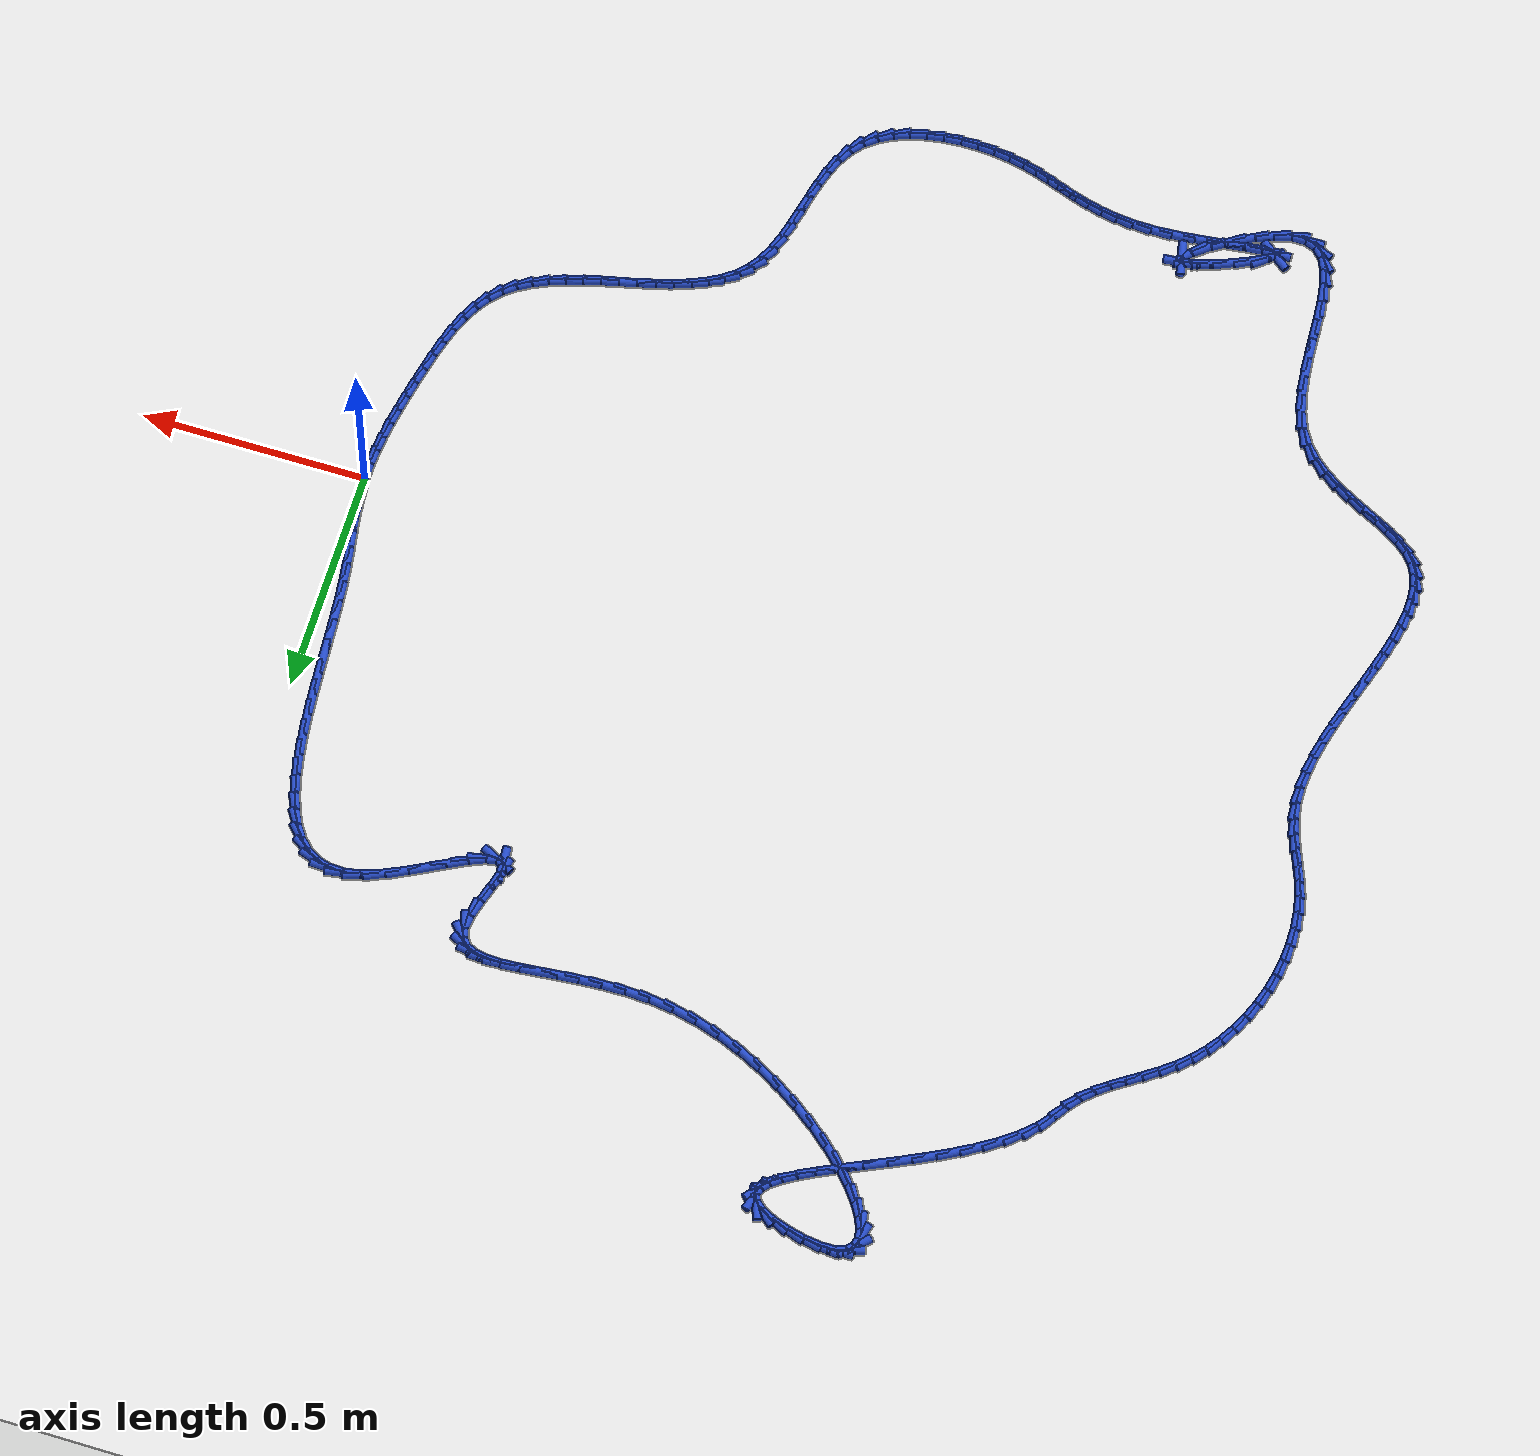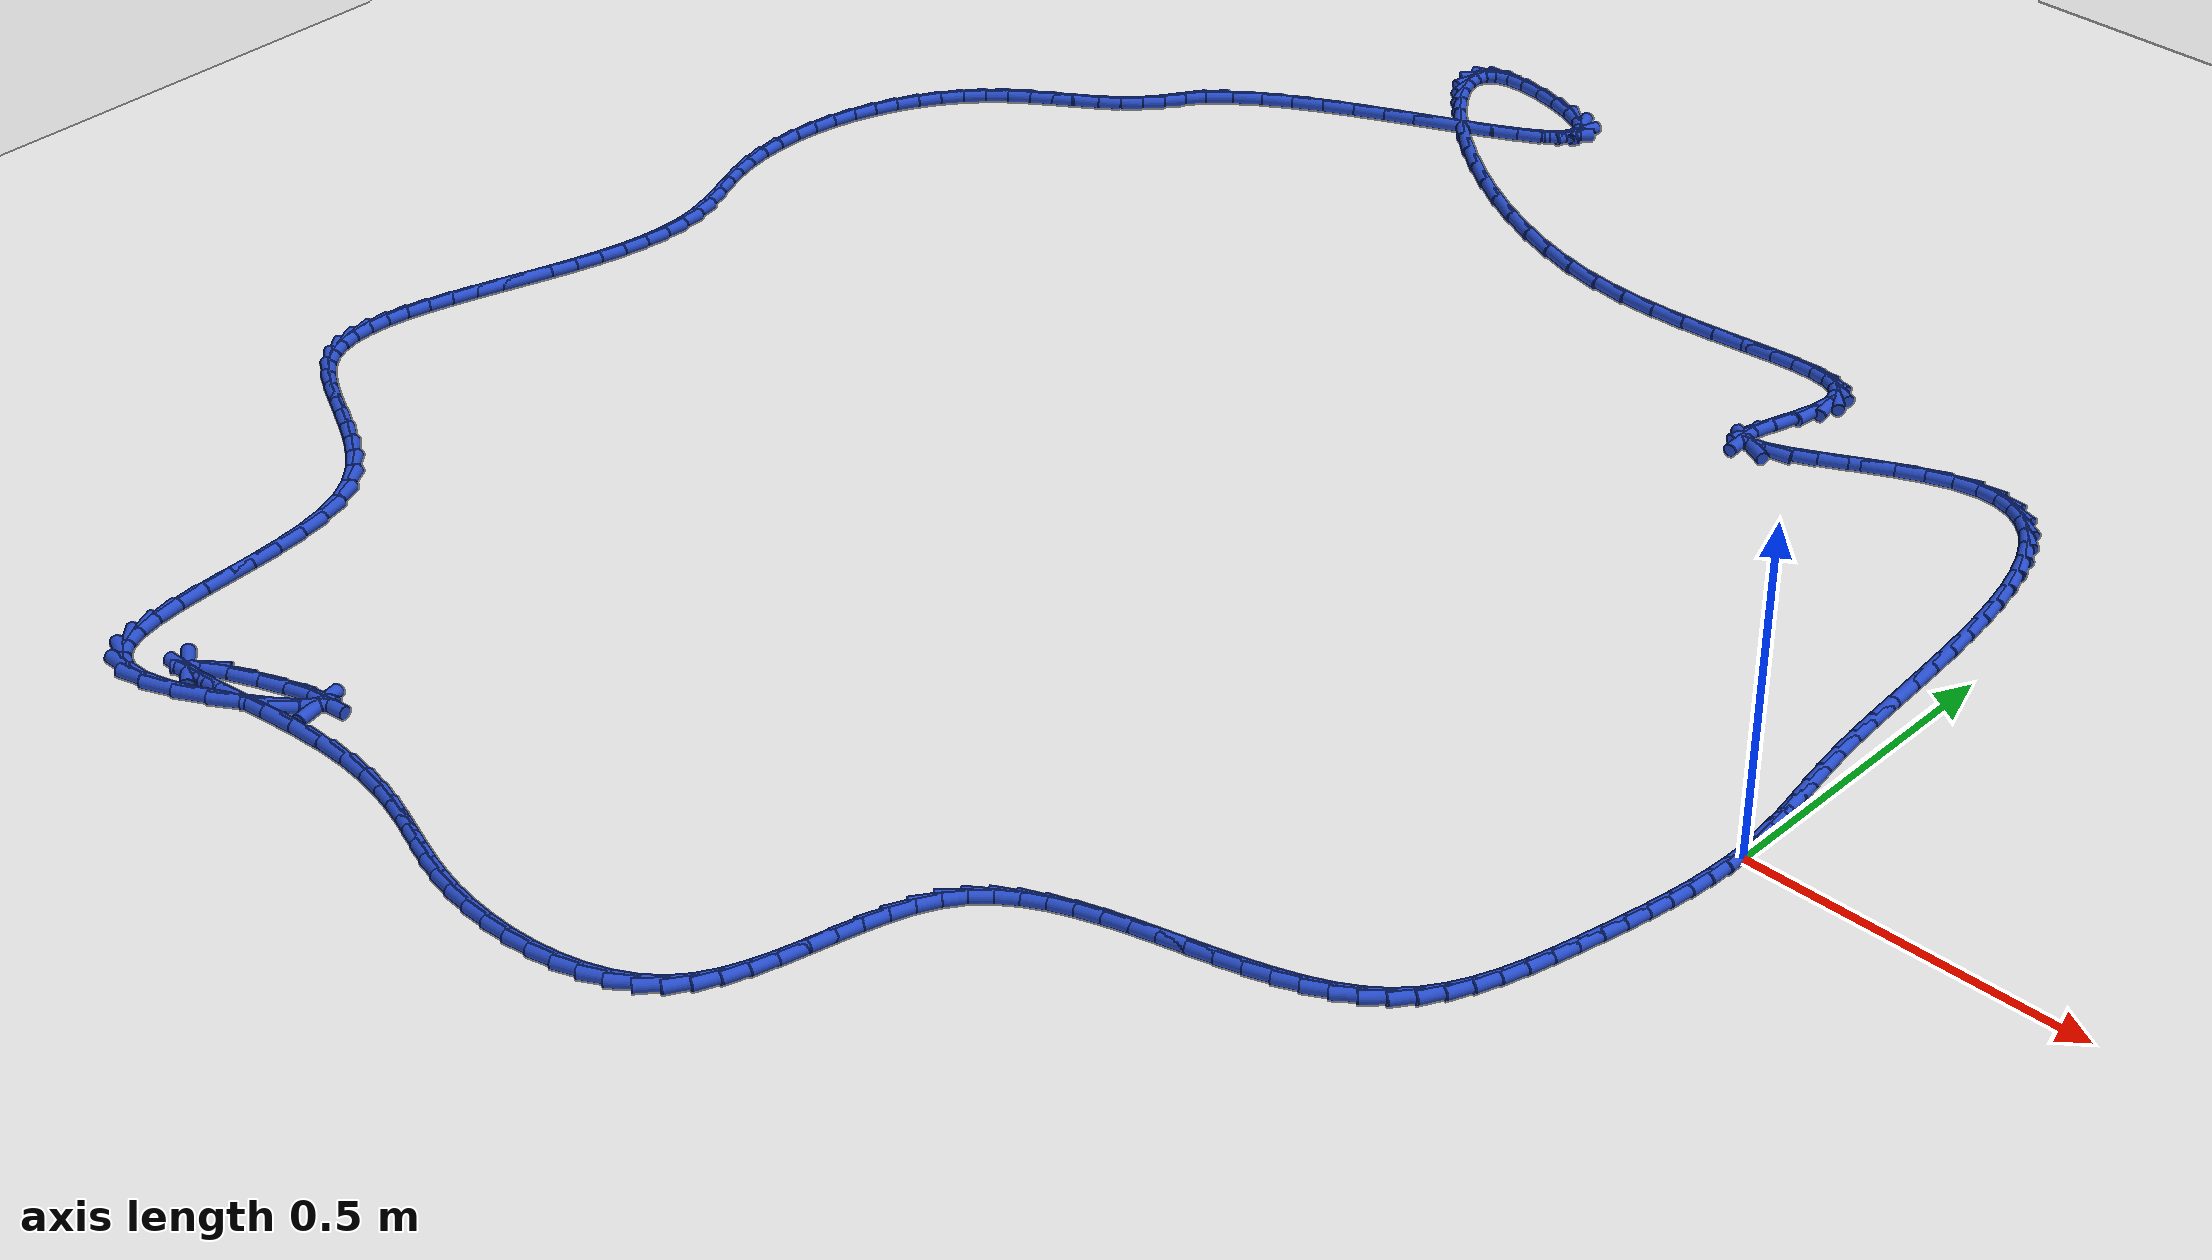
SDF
<sdf version="1.6">
 <world name="default">
  <light name="sun" type="directional">
   <pose>0 0 10 0 -0 0</pose>
   <diffuse>0.8 0.8 0.8 1</diffuse>
   <specular>0.2 0.2 0.2 1</specular>
   <attenuation>
    <range>1000</range>
    <constant>0.9</constant>
    <linear>0.01</linear>
    <quadratic>0.001</quadratic>
   </attenuation>
   <direction>-0.5 0.1 -0.9</direction>
  </light>
  <model name="ground_plane">
   <static>1</static>
   <link name="link">
    <collision name="collision">
     <geometry><plane><normal>0 0 1</normal><size>100 100</size></plane></geometry>
     <surface><friction><ode><mu>100</mu><mu2>50</mu2></ode></friction></surface>
    </collision>
    <visual name="visual">
     <cast_shadows>0</cast_shadows>
     <geometry><plane><normal>0 0 1</normal><size>100 100</size></plane></geometry>
     <material>
      <script><uri>file://media/materials/scripts/gazebo.material</uri><name>Gazebo/WhiteGlow</name></script>
     </material>
    </visual>
   </link>
  </model>
  <gravity>0 0 -9.8</gravity>
  <magnetic_field>6e-06 2.3e-05 -4.2e-05</magnetic_field>
  <atmosphere type="adiabatic"/>
  <physics name="default_physics" default="0" type="ode">
   <max_step_size>0.001</max_step_size>
   <real_time_factor>1</real_time_factor>
   <real_time_update_rate>1000</real_time_update_rate>
  </physics>
  <scene><ambient>0.4 0.4 0.4 1</ambient><background>0.7 0.7 0.7 1</background><shadows>1</shadows></scene>
  <spherical_coordinates>
   <surface_model>EARTH_WGS84</surface_model>
   <latitude_deg>0</latitude_deg>
   <longitude_deg>0</longitude_deg>
   <elevation>0</elevation>
   <heading_deg>0</heading_deg>
  </spherical_coordinates>
  <model name="line">
   <link name="link_0">
    <pose>-6.938893903907228e-18 -6.938893903907228e-18 0.01 0 1.57 -1.5177969612141762</pose>
    <collision name="collision">
     <geometry><cylinder><radius>0.01</radius><length>0.08</length></cylinder></geometry>
    </collision>
    <visual name="visual">
     <material>
      <script><name>Gazebo/Blue</name><uri>file://media/materials/scripts/gazebo.material</uri></script>
     </material>
     <geometry><cylinder><radius>0.01</radius><length>0.08</length></cylinder></geometry>
    </visual>
   </link>
   <link name="link_1">
    <pose>-0.0017515799302486427 0.0330181235278298 0.01 0 1.57 -1.4679844494604115</pose>
    <collision name="collision">
     <geometry><cylinder><radius>0.01</radius><length>0.08</length></cylinder></geometry>
    </collision>
    <visual name="visual">
     <material>
      <script><name>Gazebo/Blue</name><uri>file://media/materials/scripts/gazebo.material</uri></script>
     </material>
     <geometry><cylinder><radius>0.01</radius><length>0.08</length></cylinder></geometry>
    </visual>
   </link>
   <link name="link_2">
    <pose>-0.005141537717968325 0.06587429909623252 0.01 0 1.57 -1.4324427644684208</pose>
    <collision name="collision">
     <geometry><cylinder><radius>0.01</radius><length>0.08</length></cylinder></geometry>
    </collision>
    <visual name="visual">
     <material>
      <script><name>Gazebo/Blue</name><uri>file://media/materials/scripts/gazebo.material</uri></script>
     </material>
     <geometry><cylinder><radius>0.01</radius><length>0.08</length></cylinder></geometry>
    </visual>
   </link>
   <link name="link_3">
    <pose>-0.009760357688056033 0.09904519484243182 0.01 0 1.57 -1.4120204576833575</pose>
    <collision name="collision">
     <geometry><cylinder><radius>0.01</radius><length>0.08</length></cylinder></geometry>
    </collision>
    <visual name="visual">
     <material>
      <script><name>Gazebo/Blue</name><uri>file://media/materials/scripts/gazebo.material</uri></script>
     </material>
     <geometry><cylinder><radius>0.01</radius><length>0.08</length></cylinder></geometry>
    </visual>
   </link>
   <link name="link_4">
    <pose>-0.015198524165408756 0.1330074789036513 0.01 0 1.57 -1.4063029760364756</pose>
    <collision name="collision">
     <geometry><cylinder><radius>0.01</radius><length>0.08</length></cylinder></geometry>
    </collision>
    <visual name="visual">
     <material>
      <script><name>Gazebo/Blue</name><uri>file://media/materials/scripts/gazebo.material</uri></script>
     </material>
     <geometry><cylinder><radius>0.01</radius><length>0.08</length></cylinder></geometry>
    </visual>
   </link>
   <link name="link_5">
    <pose>-0.021046521474923478 0.16823781941711455 0.01 0 1.57 -1.4139267796736377</pose>
    <collision name="collision">
     <geometry><cylinder><radius>0.01</radius><length>0.08</length></cylinder></geometry>
    </collision>
    <visual name="visual">
     <material>
      <script><name>Gazebo/Blue</name><uri>file://media/materials/scripts/gazebo.material</uri></script>
     </material>
     <geometry><cylinder><radius>0.01</radius><length>0.08</length></cylinder></geometry>
    </visual>
   </link>
   <link name="link_6">
    <pose>-0.02689483394149718 0.20521288452004527 0.01 0 1.57 -1.4329114620557057</pose>
    <collision name="collision">
     <geometry><cylinder><radius>0.01</radius><length>0.08</length></cylinder></geometry>
    </collision>
    <visual name="visual">
     <material>
      <script><name>Gazebo/Blue</name><uri>file://media/materials/scripts/gazebo.material</uri></script>
     </material>
     <geometry><cylinder><radius>0.01</radius><length>0.08</length></cylinder></geometry>
    </visual>
   </link>
   <link name="link_7">
    <pose>-0.03233394589002684 0.24440934234966696 0.01 0 1.57 -1.4600661538370552</pose>
    <collision name="collision">
     <geometry><cylinder><radius>0.01</radius><length>0.08</length></cylinder></geometry>
    </collision>
    <visual name="visual">
     <material>
      <script><name>Gazebo/Blue</name><uri>file://media/materials/scripts/gazebo.material</uri></script>
     </material>
     <geometry><cylinder><radius>0.01</radius><length>0.08</length></cylinder></geometry>
    </visual>
   </link>
   <link name="link_8">
    <pose>-0.036986519967477004 0.2862546953946999 0.01 0 1.57 -1.4832499196775513</pose>
    <collision name="collision">
     <geometry><cylinder><radius>0.01</radius><length>0.08</length></cylinder></geometry>
    </collision>
    <visual name="visual">
     <material>
      <script><name>Gazebo/Blue</name><uri>file://media/materials/scripts/gazebo.material</uri></script>
     </material>
     <geometry><cylinder><radius>0.01</radius><length>0.08</length></cylinder></geometry>
    </visual>
   </link>
   <link name="link_9">
    <pose>-0.040875637517500445 0.33056464156144416 0.01 0 1.57 -1.4968625900266792</pose>
    <collision name="collision">
     <geometry><cylinder><radius>0.01</radius><length>0.08</length></cylinder></geometry>
    </collision>
    <visual name="visual">
     <material>
      <script><name>Gazebo/Blue</name><uri>file://media/materials/scripts/gazebo.material</uri></script>
     </material>
     <geometry><cylinder><radius>0.01</radius><length>0.08</length></cylinder></geometry>
    </visual>
   </link>
   <link name="link_10">
    <pose>-0.04429580100148908 0.37674017113896774 0.01 0 1.57 -1.502369246488138</pose>
    <collision name="collision">
     <geometry><cylinder><radius>0.01</radius><length>0.08</length></cylinder></geometry>
    </collision>
    <visual name="visual">
     <material>
      <script><name>Gazebo/Blue</name><uri>file://media/materials/scripts/gazebo.material</uri></script>
     </material>
     <geometry><cylinder><radius>0.01</radius><length>0.08</length></cylinder></geometry>
    </visual>
   </link>
   <link name="link_11">
    <pose>-0.04754666259062296 0.42417440611230545 0.01 0 1.57 -1.500596032181259</pose>
    <collision name="collision">
     <geometry><cylinder><radius>0.01</radius><length>0.08</length></cylinder></geometry>
    </collision>
    <visual name="visual">
     <material>
      <script><name>Gazebo/Blue</name><uri>file://media/materials/scripts/gazebo.material</uri></script>
     </material>
     <geometry><cylinder><radius>0.01</radius><length>0.08</length></cylinder></geometry>
    </visual>
   </link>
   <link name="link_12">
    <pose>-0.05092787445608198 0.4722604684664915 0.01 0 1.57 -1.4917770333347309</pose>
    <collision name="collision">
     <geometry><cylinder><radius>0.01</radius><length>0.08</length></cylinder></geometry>
    </collision>
    <visual name="visual">
     <material>
      <script><name>Gazebo/Blue</name><uri>file://media/materials/scripts/gazebo.material</uri></script>
     </material>
     <geometry><cylinder><radius>0.01</radius><length>0.08</length></cylinder></geometry>
    </visual>
   </link>
   <link name="link_13">
    <pose>-0.054739088769046186 0.52039148018656 0.01 0 1.57 -1.4756262927464154</pose>
    <collision name="collision">
     <geometry><cylinder><radius>0.01</radius><length>0.08</length></cylinder></geometry>
    </collision>
    <visual name="visual">
     <material>
      <script><name>Gazebo/Blue</name><uri>file://media/materials/scripts/gazebo.material</uri></script>
     </material>
     <geometry><cylinder><radius>0.01</radius><length>0.08</length></cylinder></geometry>
    </visual>
   </link>
   <link name="link_14">
    <pose>-0.05927995770069553 0.5679605632575454 0.01 0 1.57 -1.4513218810831165</pose>
    <collision name="collision">
     <geometry><cylinder><radius>0.01</radius><length>0.08</length></cylinder></geometry>
    </collision>
    <visual name="visual">
     <material>
      <script><name>Gazebo/Blue</name><uri>file://media/materials/scripts/gazebo.material</uri></script>
     </material>
     <geometry><cylinder><radius>0.01</radius><length>0.08</length></cylinder></geometry>
    </visual>
   </link>
   <link name="link_15">
    <pose>-0.06485013342221006 0.6143608396644825 0.01 0 1.57 -1.417406883829234</pose>
    <collision name="collision">
     <geometry><cylinder><radius>0.01</radius><length>0.08</length></cylinder></geometry>
    </collision>
    <visual name="visual">
     <material>
      <script><name>Gazebo/Blue</name><uri>file://media/materials/scripts/gazebo.material</uri></script>
     </material>
     <geometry><cylinder><radius>0.01</radius><length>0.08</length></cylinder></geometry>
    </visual>
   </link>
   <link name="link_16">
    <pose>-0.07174926810476971 0.6589854313924051 0.01 0 1.57 -1.3715954360244975</pose>
    <collision name="collision">
     <geometry><cylinder><radius>0.01</radius><length>0.08</length></cylinder></geometry>
    </collision>
    <visual name="visual">
     <material>
      <script><name>Gazebo/Blue</name><uri>file://media/materials/scripts/gazebo.material</uri></script>
     </material>
     <geometry><cylinder><radius>0.01</radius><length>0.08</length></cylinder></geometry>
    </visual>
   </link>
   <link name="link_17">
    <pose>-0.08027701391955447 0.7012274604263474 0.01 0 1.57 -1.3104638574253555</pose>
    <collision name="collision">
     <geometry><cylinder><radius>0.01</radius><length>0.08</length></cylinder></geometry>
    </collision>
    <visual name="visual">
     <material>
      <script><name>Gazebo/Blue</name><uri>file://media/materials/scripts/gazebo.material</uri></script>
     </material>
     <geometry><cylinder><radius>0.01</radius><length>0.08</length></cylinder></geometry>
    </visual>
   </link>
   <link name="link_18">
    <pose>-0.09073302303774436 0.7404800487513445 0.01 0 1.57 -1.2290279747981148</pose>
    <collision name="collision">
     <geometry><cylinder><radius>0.01</radius><length>0.08</length></cylinder></geometry>
    </collision>
    <visual name="visual">
     <material>
      <script><name>Gazebo/Blue</name><uri>file://media/materials/scripts/gazebo.material</uri></script>
     </material>
     <geometry><cylinder><radius>0.01</radius><length>0.08</length></cylinder></geometry>
    </visual>
   </link>
   <link name="link_19">
    <pose>-0.10341694763051931 0.7761363183524299 0.01 0 1.57 -1.1203343275249618</pose>
    <collision name="collision">
     <geometry><cylinder><radius>0.01</radius><length>0.08</length></cylinder></geometry>
    </collision>
    <visual name="visual">
     <material>
      <script><name>Gazebo/Blue</name><uri>file://media/materials/scripts/gazebo.material</uri></script>
     </material>
     <geometry><cylinder><radius>0.01</radius><length>0.08</length></cylinder></geometry>
    </visual>
   </link>
   <link name="link_20">
    <pose>-0.11862843986905935 0.8075893912146389 0.01 0 1.57 -0.9756378624648923</pose>
    <collision name="collision">
     <geometry><cylinder><radius>0.01</radius><length>0.08</length></cylinder></geometry>
    </collision>
    <visual name="visual">
     <material>
      <script><name>Gazebo/Blue</name><uri>file://media/materials/scripts/gazebo.material</uri></script>
     </material>
     <geometry><cylinder><radius>0.01</radius><length>0.08</length></cylinder></geometry>
    </visual>
   </link>
   <link name="link_21">
    <pose>-0.13666715192454448 0.834232389323005 0.01 0 1.57 -0.7868244179630445</pose>
    <collision name="collision">
     <geometry><cylinder><radius>0.01</radius><length>0.08</length></cylinder></geometry>
    </collision>
    <visual name="visual">
     <material>
      <script><name>Gazebo/Blue</name><uri>file://media/materials/scripts/gazebo.material</uri></script>
     </material>
     <geometry><cylinder><radius>0.01</radius><length>0.08</length></cylinder></geometry>
    </visual>
   </link>
   <link name="link_22">
    <pose>-0.1578327359681547 0.8554584346625629 0.01 0 1.57 -0.5536760380981668</pose>
    <collision name="collision">
     <geometry><cylinder><radius>0.01</radius><length>0.08</length></cylinder></geometry>
    </collision>
    <visual name="visual">
     <material>
      <script><name>Gazebo/Blue</name><uri>file://media/materials/scripts/gazebo.material</uri></script>
     </material>
     <geometry><cylinder><radius>0.01</radius><length>0.08</length></cylinder></geometry>
    </visual>
   </link>
   <link name="link_23">
    <pose>-0.18242484417106986 0.8706606492183468 0.01 0 1.57 -0.2939178139863472</pose>
    <collision name="collision">
     <geometry><cylinder><radius>0.01</radius><length>0.08</length></cylinder></geometry>
    </collision>
    <visual name="visual">
     <material>
      <script><name>Gazebo/Blue</name><uri>file://media/materials/scripts/gazebo.material</uri></script>
     </material>
     <geometry><cylinder><radius>0.01</radius><length>0.08</length></cylinder></geometry>
    </visual>
   </link>
   <link name="link_24">
    <pose>-0.2107431287044702 0.8792321549753914 0.01 0 1.57 -0.04121811728965706</pose>
    <collision name="collision">
     <geometry><cylinder><radius>0.01</radius><length>0.08</length></cylinder></geometry>
    </collision>
    <visual name="visual">
     <material>
      <script><name>Gazebo/Blue</name><uri>file://media/materials/scripts/gazebo.material</uri></script>
     </material>
     <geometry><cylinder><radius>0.01</radius><length>0.08</length></cylinder></geometry>
    </visual>
   </link>
   <link name="link_25">
    <pose>-0.24308724173953547 0.8805660739187308 0.01 0 1.57 0.1757151035363333</pose>
    <collision name="collision">
     <geometry><cylinder><radius>0.01</radius><length>0.08</length></cylinder></geometry>
    </collision>
    <visual name="visual">
     <material>
      <script><name>Gazebo/Blue</name><uri>file://media/materials/scripts/gazebo.material</uri></script>
     </material>
     <geometry><cylinder><radius>0.01</radius><length>0.08</length></cylinder></geometry>
    </visual>
   </link>
   <link name="link_26">
    <pose>-0.27975683544744584 0.8740555280333993 0.01 0 1.57 0.3384609954954084</pose>
    <collision name="collision">
     <geometry><cylinder><radius>0.01</radius><length>0.08</length></cylinder></geometry>
    </collision>
    <visual name="visual">
     <material>
      <script><name>Gazebo/Blue</name><uri>file://media/materials/scripts/gazebo.material</uri></script>
     </material>
     <geometry><cylinder><radius>0.01</radius><length>0.08</length></cylinder></geometry>
    </visual>
   </link>
   <link name="link_27">
    <pose>-0.32065855699211976 0.8596578668622273 0.01 0 1.57 0.4316609335593668</pose>
    <collision name="collision">
     <geometry><cylinder><radius>0.01</radius><length>0.08</length></cylinder></geometry>
    </collision>
    <visual name="visual">
     <material>
      <script><name>Gazebo/Blue</name><uri>file://media/materials/scripts/gazebo.material</uri></script>
     </material>
     <geometry><cylinder><radius>0.01</radius><length>0.08</length></cylinder></geometry>
    </visual>
   </link>
   <link name="link_28">
    <pose>-0.36407830859653223 0.8396573033287732 0.01 0 1.57 0.4784481100144128</pose>
    <collision name="collision">
     <geometry><cylinder><radius>0.01</radius><length>0.08</length></cylinder></geometry>
    </collision>
    <visual name="visual">
     <material>
      <script><name>Gazebo/Blue</name><uri>file://media/materials/scripts/gazebo.material</uri></script>
     </material>
     <geometry><cylinder><radius>0.01</radius><length>0.08</length></cylinder></geometry>
    </visual>
   </link>
   <link name="link_29">
    <pose>-0.40788424982599303 0.816937793146551 0.01 0 1.57 0.49221924320158916</pose>
    <collision name="collision">
     <geometry><cylinder><radius>0.01</radius><length>0.08</length></cylinder></geometry>
    </collision>
    <visual name="visual">
     <material>
      <script><name>Gazebo/Blue</name><uri>file://media/materials/scripts/gazebo.material</uri></script>
     </material>
     <geometry><cylinder><radius>0.01</radius><length>0.08</length></cylinder></geometry>
    </visual>
   </link>
   <link name="link_30">
    <pose>-0.44994453981901295 0.7943832926418193 0.01 0 1.57 0.4722868155899715</pose>
    <collision name="collision">
     <geometry><cylinder><radius>0.01</radius><length>0.08</length></cylinder></geometry>
    </collision>
    <visual name="visual">
     <material>
      <script><name>Gazebo/Blue</name><uri>file://media/materials/scripts/gazebo.material</uri></script>
     </material>
     <geometry><cylinder><radius>0.01</radius><length>0.08</length></cylinder></geometry>
    </visual>
   </link>
   <link name="link_31">
    <pose>-0.4881273377141033 0.7748777581408365 0.01 0 1.57 0.39920577333253987</pose>
    <collision name="collision">
     <geometry><cylinder><radius>0.01</radius><length>0.08</length></cylinder></geometry>
    </collision>
    <visual name="visual">
     <material>
      <script><name>Gazebo/Blue</name><uri>file://media/materials/scripts/gazebo.material</uri></script>
     </material>
     <geometry><cylinder><radius>0.01</radius><length>0.08</length></cylinder></geometry>
    </visual>
   </link>
   <link name="link_32">
    <pose>-0.5203008026497754 0.7613051459698613 0.01 0 1.57 0.1953652292399074</pose>
    <collision name="collision">
     <geometry><cylinder><radius>0.01</radius><length>0.08</length></cylinder></geometry>
    </collision>
    <visual name="visual">
     <material>
      <script><name>Gazebo/Blue</name><uri>file://media/materials/scripts/gazebo.material</uri></script>
     </material>
     <geometry><cylinder><radius>0.01</radius><length>0.08</length></cylinder></geometry>
    </visual>
   </link>
   <link name="link_33">
    <pose>-0.5443330937645399 0.756549412455152 0.01 0 1.57 -0.4674465640434654</pose>
    <collision name="collision">
     <geometry><cylinder><radius>0.01</radius><length>0.08</length></cylinder></geometry>
    </collision>
    <visual name="visual">
     <material>
      <script><name>Gazebo/Blue</name><uri>file://media/materials/scripts/gazebo.material</uri></script>
     </material>
     <geometry><cylinder><radius>0.01</radius><length>0.08</length></cylinder></geometry>
    </visual>
   </link>
   <link name="link_34">
    <pose>-0.5580923701969078 0.763494513922967 0.01 0 1.57 -1.4948324538092168</pose>
    <collision name="collision">
     <geometry><cylinder><radius>0.01</radius><length>0.08</length></cylinder></geometry>
    </collision>
    <visual name="visual">
     <material>
      <script><name>Gazebo/Blue</name><uri>file://media/materials/scripts/gazebo.material</uri></script>
     </material>
     <geometry><cylinder><radius>0.01</radius><length>0.08</length></cylinder></geometry>
    </visual>
   </link>
   <link name="link_35">
    <pose>-0.5597076829982736 0.7847178202460561 0.01 0 1.57 1.328714973944007</pose>
    <collision name="collision">
     <geometry><cylinder><radius>0.01</radius><length>0.08</length></cylinder></geometry>
    </collision>
    <visual name="visual">
     <material>
      <script><name>Gazebo/Blue</name><uri>file://media/materials/scripts/gazebo.material</uri></script>
     </material>
     <geometry><cylinder><radius>0.01</radius><length>0.08</length></cylinder></geometry>
    </visual>
   </link>
   <link name="link_36">
    <pose>-0.551530255745919 0.8178350262244877 0.01 0 1.57 1.2647704939799607</pose>
    <collision name="collision">
     <geometry><cylinder><radius>0.01</radius><length>0.08</length></cylinder></geometry>
    </collision>
    <visual name="visual">
     <material>
      <script><name>Gazebo/Blue</name><uri>file://media/materials/scripts/gazebo.material</uri></script>
     </material>
     <geometry><cylinder><radius>0.01</radius><length>0.08</length></cylinder></geometry>
    </visual>
   </link>
   <link name="link_37">
    <pose>-0.5393325337056601 0.8564413868809333 0.01 0 1.57 1.3020848104628495</pose>
    <collision name="collision">
     <geometry><cylinder><radius>0.01</radius><length>0.08</length></cylinder></geometry>
    </collision>
    <visual name="visual">
     <material>
      <script><name>Gazebo/Blue</name><uri>file://media/materials/scripts/gazebo.material</uri></script>
     </material>
     <geometry><cylinder><radius>0.01</radius><length>0.08</length></cylinder></geometry>
    </visual>
   </link>
   <link name="link_38">
    <pose>-0.5289854386543372 0.8940164328220209 0.01 0 1.57 1.4684994391314454</pose>
    <collision name="collision">
     <geometry><cylinder><radius>0.01</radius><length>0.08</length></cylinder></geometry>
    </collision>
    <visual name="visual">
     <material>
      <script><name>Gazebo/Blue</name><uri>file://media/materials/scripts/gazebo.material</uri></script>
     </material>
     <geometry><cylinder><radius>0.01</radius><length>0.08</length></cylinder></geometry>
    </visual>
   </link>
   <link name="link_39">
    <pose>-0.5258416901231799 0.9246407740435671 0.01 0 1.57 -1.337919915060785</pose>
    <collision name="collision">
     <geometry><cylinder><radius>0.01</radius><length>0.08</length></cylinder></geometry>
    </collision>
    <visual name="visual">
     <material>
      <script><name>Gazebo/Blue</name><uri>file://media/materials/scripts/gazebo.material</uri></script>
     </material>
     <geometry><cylinder><radius>0.01</radius><length>0.08</length></cylinder></geometry>
    </visual>
   </link>
   <link name="link_40">
    <pose>-0.5311748574808346 0.9471265575212082 0.01 0 1.57 -0.8638906822429644</pose>
    <collision name="collision">
     <geometry><cylinder><radius>0.01</radius><length>0.08</length></cylinder></geometry>
    </collision>
    <visual name="visual">
     <material>
      <script><name>Gazebo/Blue</name><uri>file://media/materials/scripts/gazebo.material</uri></script>
     </material>
     <geometry><cylinder><radius>0.01</radius><length>0.08</length></cylinder></geometry>
    </visual>
   </link>
   <link name="link_41">
    <pose>-0.5443278956909156 0.9625253117407232 0.01 0 1.57 -0.4326267000269725</pose>
    <collision name="collision">
     <geometry><cylinder><radius>0.01</radius><length>0.08</length></cylinder></geometry>
    </collision>
    <visual name="visual">
     <material>
      <script><name>Gazebo/Blue</name><uri>file://media/materials/scripts/gazebo.material</uri></script>
     </material>
     <geometry><cylinder><radius>0.01</radius><length>0.08</length></cylinder></geometry>
    </visual>
   </link>
   <link name="link_42">
    <pose>-0.5646322320761914 0.9719019364678838 0.01 0 1.57 -0.1635095303750284</pose>
    <collision name="collision">
     <geometry><cylinder><radius>0.01</radius><length>0.08</length></cylinder></geometry>
    </collision>
    <visual name="visual">
     <material>
      <script><name>Gazebo/Blue</name><uri>file://media/materials/scripts/gazebo.material</uri></script>
     </material>
     <geometry><cylinder><radius>0.01</radius><length>0.08</length></cylinder></geometry>
    </visual>
   </link>
   <link name="link_43">
    <pose>-0.5914192939594306 0.9763213314684609 0.01 0 1.57 -0.016165628537023982</pose>
    <collision name="collision">
     <geometry><cylinder><radius>0.01</radius><length>0.08</length></cylinder></geometry>
    </collision>
    <visual name="visual">
     <material>
      <script><name>Gazebo/Blue</name><uri>file://media/materials/scripts/gazebo.material</uri></script>
     </material>
     <geometry><cylinder><radius>0.01</radius><length>0.08</length></cylinder></geometry>
    </visual>
   </link>
   <link name="link_44">
    <pose>-0.624020508663401 0.9768483965082254 0.01 0 1.57 0.06086672252184156</pose>
    <collision name="collision">
     <geometry><cylinder><radius>0.01</radius><length>0.08</length></cylinder></geometry>
    </collision>
    <visual name="visual">
     <material>
      <script><name>Gazebo/Blue</name><uri>file://media/materials/scripts/gazebo.material</uri></script>
     </material>
     <geometry><cylinder><radius>0.01</radius><length>0.08</length></cylinder></geometry>
    </visual>
   </link>
   <link name="link_45">
    <pose>-0.6617673035108715 0.9745480313529493 0.01 0 1.57 0.09592754155805806</pose>
    <collision name="collision">
     <geometry><cylinder><radius>0.01</radius><length>0.08</length></cylinder></geometry>
    </collision>
    <visual name="visual">
     <material>
      <script><name>Gazebo/Blue</name><uri>file://media/materials/scripts/gazebo.material</uri></script>
     </material>
     <geometry><cylinder><radius>0.01</radius><length>0.08</length></cylinder></geometry>
    </visual>
   </link>
   <link name="link_46">
    <pose>-0.7039911058246098 0.9704851357684028 0.01 0 1.57 0.10305088690284292</pose>
    <collision name="collision">
     <geometry><cylinder><radius>0.01</radius><length>0.08</length></cylinder></geometry>
    </collision>
    <visual name="visual">
     <material>
      <script><name>Gazebo/Blue</name><uri>file://media/materials/scripts/gazebo.material</uri></script>
     </material>
     <geometry><cylinder><radius>0.01</radius><length>0.08</length></cylinder></geometry>
    </visual>
   </link>
   <link name="link_47">
    <pose>-0.7500233429273853 0.9657246095203584 0.01 0 1.57 0.08910791375788486</pose>
    <collision name="collision">
     <geometry><cylinder><radius>0.01</radius><length>0.08</length></cylinder></geometry>
    </collision>
    <visual name="visual">
     <material>
      <script><name>Gazebo/Blue</name><uri>file://media/materials/scripts/gazebo.material</uri></script>
     </material>
     <geometry><cylinder><radius>0.01</radius><length>0.08</length></cylinder></geometry>
    </visual>
   </link>
   <link name="link_48">
    <pose>-0.7991954421419653 0.9613313523745861 0.01 0 1.57 0.05727450939299723</pose>
    <collision name="collision">
     <geometry><cylinder><radius>0.01</radius><length>0.08</length></cylinder></geometry>
    </collision>
    <visual name="visual">
     <material>
      <script><name>Gazebo/Blue</name><uri>file://media/materials/scripts/gazebo.material</uri></script>
     </material>
     <geometry><cylinder><radius>0.01</radius><length>0.08</length></cylinder></geometry>
    </visual>
   </link>
   <link name="link_49">
    <pose>-0.8508388307911182 0.9583702640968579 0.01 0 1.57 0.008681792285163832</pose>
    <collision name="collision">
     <geometry><cylinder><radius>0.01</radius><length>0.08</length></cylinder></geometry>
    </collision>
    <visual name="visual">
     <material>
      <script><name>Gazebo/Blue</name><uri>file://media/materials/scripts/gazebo.material</uri></script>
     </material>
     <geometry><cylinder><radius>0.01</radius><length>0.08</length></cylinder></geometry>
    </visual>
   </link>
   <link name="link_50">
    <pose>-0.9042849361976133 0.9579062444529449 0.01 0 1.57 -0.05669868445683849</pose>
    <collision name="collision">
     <geometry><cylinder><radius>0.01</radius><length>0.08</length></cylinder></geometry>
    </collision>
    <visual name="visual">
     <material>
      <script><name>Gazebo/Blue</name><uri>file://media/materials/scripts/gazebo.material</uri></script>
     </material>
     <geometry><cylinder><radius>0.01</radius><length>0.08</length></cylinder></geometry>
    </visual>
   </link>
   <link name="link_51">
    <pose>-0.9588651856842174 0.961004193208618 0.01 0 1.57 -0.1394208972350012</pose>
    <collision name="collision">
     <geometry><cylinder><radius>0.01</radius><length>0.08</length></cylinder></geometry>
    </collision>
    <visual name="visual">
     <material>
      <script><name>Gazebo/Blue</name><uri>file://media/materials/scripts/gazebo.material</uri></script>
     </material>
     <geometry><cylinder><radius>0.01</radius><length>0.08</length></cylinder></geometry>
    </visual>
   </link>
   <link name="link_52">
    <pose>-1.0139110183002287 0.9687288486594569 0.01 0 1.57 -0.23341070814844342</pose>
    <collision name="collision">
     <geometry><cylinder><radius>0.01</radius><length>0.08</length></cylinder></geometry>
    </collision>
    <visual name="visual">
     <material>
      <script><name>Gazebo/Blue</name><uri>file://media/materials/scripts/gazebo.material</uri></script>
     </material>
     <geometry><cylinder><radius>0.01</radius><length>0.08</length></cylinder></geometry>
    </visual>
   </link>
   <link name="link_53">
    <pose>-1.0687808262712903 0.9817738132958911 0.01 0 1.57 -0.31926257511083317</pose>
    <collision name="collision">
     <geometry><cylinder><radius>0.01</radius><length>0.08</length></cylinder></geometry>
    </collision>
    <visual name="visual">
     <material>
      <script><name>Gazebo/Blue</name><uri>file://media/materials/scripts/gazebo.material</uri></script>
     </material>
     <geometry><cylinder><radius>0.01</radius><length>0.08</length></cylinder></geometry>
    </visual>
   </link>
   <link name="link_54">
    <pose>-1.1229174532601016 0.9996698228766931 0.01 0 1.57 -0.3951856956327461</pose>
    <collision name="collision">
     <geometry><cylinder><radius>0.01</radius><length>0.08</length></cylinder></geometry>
    </collision>
    <visual name="visual">
     <material>
      <script><name>Gazebo/Blue</name><uri>file://media/materials/scripts/gazebo.material</uri></script>
     </material>
     <geometry><cylinder><radius>0.01</radius><length>0.08</length></cylinder></geometry>
    </visual>
   </link>
   <link name="link_55">
    <pose>-1.1757802390551937 1.0217204672812727 0.01 0 1.57 -0.4634082291257011</pose>
    <collision name="collision">
     <geometry><cylinder><radius>0.01</radius><length>0.08</length></cylinder></geometry>
    </collision>
    <visual name="visual">
     <material>
      <script><name>Gazebo/Blue</name><uri>file://media/materials/scripts/gazebo.material</uri></script>
     </material>
     <geometry><cylinder><radius>0.01</radius><length>0.08</length></cylinder></geometry>
    </visual>
   </link>
   <link name="link_56">
    <pose>-1.2268285234450989 1.0472293363890415 0.01 0 1.57 -0.5260242978912739</pose>
    <collision name="collision">
     <geometry><cylinder><radius>0.01</radius><length>0.08</length></cylinder></geometry>
    </collision>
    <visual name="visual">
     <material>
      <script><name>Gazebo/Blue</name><uri>file://media/materials/scripts/gazebo.material</uri></script>
     </material>
     <geometry><cylinder><radius>0.01</radius><length>0.08</length></cylinder></geometry>
    </visual>
   </link>
   <link name="link_57">
    <pose>-1.2755216462183478 1.0755000200794074 0.01 0 1.57 -0.5850422700894921</pose>
    <collision name="collision">
     <geometry><cylinder><radius>0.01</radius><length>0.08</length></cylinder></geometry>
    </collision>
    <visual name="visual">
     <material>
      <script><name>Gazebo/Blue</name><uri>file://media/materials/scripts/gazebo.material</uri></script>
     </material>
     <geometry><cylinder><radius>0.01</radius><length>0.08</length></cylinder></geometry>
    </visual>
   </link>
   <link name="link_58">
    <pose>-1.3213189471634743 1.105836108231783 0.01 0 1.57 -0.6425103009653051</pose>
    <collision name="collision">
     <geometry><cylinder><radius>0.01</radius><length>0.08</length></cylinder></geometry>
    </collision>
    <visual name="visual">
     <material>
      <script><name>Gazebo/Blue</name><uri>file://media/materials/scripts/gazebo.material</uri></script>
     </material>
     <geometry><cylinder><radius>0.01</radius><length>0.08</length></cylinder></geometry>
    </visual>
   </link>
   <link name="link_59">
    <pose>-1.3636797660690085 1.137541190725577 0.01 0 1.57 -0.7007241162774768</pose>
    <collision name="collision">
     <geometry><cylinder><radius>0.01</radius><length>0.08</length></cylinder></geometry>
    </collision>
    <visual name="visual">
     <material>
      <script><name>Gazebo/Blue</name><uri>file://media/materials/scripts/gazebo.material</uri></script>
     </material>
     <geometry><cylinder><radius>0.01</radius><length>0.08</length></cylinder></geometry>
    </visual>
   </link>
   <link name="link_60">
    <pose>-1.4020634427234828 1.1699188574402 0.01 0 1.57 -0.7625685471487621</pose>
    <collision name="collision">
     <geometry><cylinder><radius>0.01</radius><length>0.08</length></cylinder></geometry>
    </collision>
    <visual name="visual">
     <material>
      <script><name>Gazebo/Blue</name><uri>file://media/materials/scripts/gazebo.material</uri></script>
     </material>
     <geometry><cylinder><radius>0.01</radius><length>0.08</length></cylinder></geometry>
    </visual>
   </link>
   <link name="link_61">
    <pose>-1.4359293169154286 1.202272698255062 0.01 0 1.57 -0.8321236549091593</pose>
    <collision name="collision">
     <geometry><cylinder><radius>0.01</radius><length>0.08</length></cylinder></geometry>
    </collision>
    <visual name="visual">
     <material>
      <script><name>Gazebo/Blue</name><uri>file://media/materials/scripts/gazebo.material</uri></script>
     </material>
     <geometry><cylinder><radius>0.01</radius><length>0.08</length></cylinder></geometry>
    </visual>
   </link>
   <link name="link_62">
    <pose>-1.4647367284333779 1.2339063030495734 0.01 0 1.57 -0.9158397496082105</pose>
    <collision name="collision">
     <geometry><cylinder><radius>0.01</radius><length>0.08</length></cylinder></geometry>
    </collision>
    <visual name="visual">
     <material>
      <script><name>Gazebo/Blue</name><uri>file://media/materials/scripts/gazebo.material</uri></script>
     </material>
     <geometry><cylinder><radius>0.01</radius><length>0.08</length></cylinder></geometry>
    </visual>
   </link>
   <link name="link_63">
    <pose>-1.487945017065864 1.2641232617031455 0.01 0 1.57 -1.0250003215539008</pose>
    <collision name="collision">
     <geometry><cylinder><radius>0.01</radius><length>0.08</length></cylinder></geometry>
    </collision>
    <visual name="visual">
     <material>
      <script><name>Gazebo/Blue</name><uri>file://media/materials/scripts/gazebo.material</uri></script>
     </material>
     <geometry><cylinder><radius>0.01</radius><length>0.08</length></cylinder></geometry>
    </visual>
   </link>
   <link name="link_64">
    <pose>-1.5050135226014159 1.2922271640951863 0.01 0 1.57 -1.181112246915442</pose>
    <collision name="collision">
     <geometry><cylinder><radius>0.01</radius><length>0.08</length></cylinder></geometry>
    </collision>
    <visual name="visual">
     <material>
      <script><name>Gazebo/Blue</name><uri>file://media/materials/scripts/gazebo.material</uri></script>
     </material>
     <geometry><cylinder><radius>0.01</radius><length>0.08</length></cylinder></geometry>
    </visual>
   </link>
   <link name="link_65">
    <pose>-1.5154015848285676 1.3175216001051075 0.01 0 1.57 -1.4264575076706398</pose>
    <collision name="collision">
     <geometry><cylinder><radius>0.01</radius><length>0.08</length></cylinder></geometry>
    </collision>
    <visual name="visual">
     <material>
      <script><name>Gazebo/Blue</name><uri>file://media/materials/scripts/gazebo.material</uri></script>
     </material>
     <geometry><cylinder><radius>0.01</radius><length>0.08</length></cylinder></geometry>
    </visual>
   </link>
   <link name="link_66">
    <pose>-1.5185685435358498 1.3393101596123196 0.01 0 1.57 1.3152369495499046</pose>
    <collision name="collision">
     <geometry><cylinder><radius>0.01</radius><length>0.08</length></cylinder></geometry>
    </collision>
    <visual name="visual">
     <material>
      <script><name>Gazebo/Blue</name><uri>file://media/materials/scripts/gazebo.material</uri></script>
     </material>
     <geometry><cylinder><radius>0.01</radius><length>0.08</length></cylinder></geometry>
    </visual>
   </link>
   <link name="link_67">
    <pose>-1.513973738511795 1.3568964324962312 0.01 0 1.57 0.7772039194500694</pose>
    <collision name="collision">
     <geometry><cylinder><radius>0.01</radius><length>0.08</length></cylinder></geometry>
    </collision>
    <visual name="visual">
     <material>
      <script><name>Gazebo/Blue</name><uri>file://media/materials/scripts/gazebo.material</uri></script>
     </material>
     <geometry><cylinder><radius>0.01</radius><length>0.08</length></cylinder></geometry>
    </visual>
   </link>
   <link name="link_68">
    <pose>-1.501076509544935 1.3695840086362543 0.01 0 1.57 0.31534926616459</pose>
    <collision name="collision">
     <geometry><cylinder><radius>0.01</radius><length>0.08</length></cylinder></geometry>
    </collision>
    <visual name="visual">
     <material>
      <script><name>Gazebo/Blue</name><uri>file://media/materials/scripts/gazebo.material</uri></script>
     </material>
     <geometry><cylinder><radius>0.01</radius><length>0.08</length></cylinder></geometry>
    </visual>
   </link>
   <link name="link_69">
    <pose>-1.4793361964238012 1.3766764779117981 0.01 0 1.57 0.029635866669905055</pose>
    <collision name="collision">
     <geometry><cylinder><radius>0.01</radius><length>0.08</length></cylinder></geometry>
    </collision>
    <visual name="visual">
     <material>
      <script><name>Gazebo/Blue</name><uri>file://media/materials/scripts/gazebo.material</uri></script>
     </material>
     <geometry><cylinder><radius>0.01</radius><length>0.08</length></cylinder></geometry>
    </visual>
   </link>
   <link name="link_70">
    <pose>-1.4485081058885136 1.3775903626585544 0.01 0 1.57 -0.1255170046728519</pose>
    <collision name="collision">
     <geometry><cylinder><radius>0.01</radius><length>0.08</length></cylinder></geometry>
    </collision>
    <visual name="visual">
     <material>
      <script><name>Gazebo/Blue</name><uri>file://media/materials/scripts/gazebo.material</uri></script>
     </material>
     <geometry><cylinder><radius>0.01</radius><length>0.08</length></cylinder></geometry>
    </visual>
   </link>
   <link name="link_71">
    <pose>-1.4114044446888037 1.372908610128369 0.01 0 1.57 -0.22828666751479357</pose>
    <collision name="collision">
     <geometry><cylinder><radius>0.01</radius><length>0.08</length></cylinder></geometry>
    </collision>
    <visual name="visual">
     <material>
      <script><name>Gazebo/Blue</name><uri>file://media/materials/scripts/gazebo.material</uri></script>
     </material>
     <geometry><cylinder><radius>0.01</radius><length>0.08</length></cylinder></geometry>
    </visual>
   </link>
   <link name="link_72">
    <pose>-1.3726414870758428 1.3639025477220934 0.01 0 1.57 -0.32483080300436346</pose>
    <collision name="collision">
     <geometry><cylinder><radius>0.01</radius><length>0.08</length></cylinder></geometry>
    </collision>
    <visual name="visual">
     <material>
      <script><name>Gazebo/Blue</name><uri>file://media/materials/scripts/gazebo.material</uri></script>
     </material>
     <geometry><cylinder><radius>0.01</radius><length>0.08</length></cylinder></geometry>
    </visual>
   </link>
   <link name="link_73">
    <pose>-1.336858850204935 1.3518524098198406 0.01 0 1.57 -0.45602378055793685</pose>
    <collision name="collision">
     <geometry><cylinder><radius>0.01</radius><length>0.08</length></cylinder></geometry>
    </collision>
    <visual name="visual">
     <material>
      <script><name>Gazebo/Blue</name><uri>file://media/materials/scripts/gazebo.material</uri></script>
     </material>
     <geometry><cylinder><radius>0.01</radius><length>0.08</length></cylinder></geometry>
    </visual>
   </link>
   <link name="link_74">
    <pose>-1.3086961512313853 1.3380384308017252 0.01 0 1.57 -0.7119718156792585</pose>
    <collision name="collision">
     <geometry><cylinder><radius>0.01</radius><length>0.08</length></cylinder></geometry>
    </collision>
    <visual name="visual">
     <material>
      <script><name>Gazebo/Blue</name><uri>file://media/materials/scripts/gazebo.material</uri></script>
     </material>
     <geometry><cylinder><radius>0.01</radius><length>0.08</length></cylinder></geometry>
    </visual>
   </link>
   <link name="link_75">
    <pose>-1.291885096465156 1.3235311114909836 0.01 0 1.57 -1.2162652560521983</pose>
    <collision name="collision">
     <geometry><cylinder><radius>0.01</radius><length>0.08</length></cylinder></geometry>
    </collision>
    <visual name="visual">
     <material>
      <script><name>Gazebo/Blue</name><uri>file://media/materials/scripts/gazebo.material</uri></script>
     </material>
     <geometry><cylinder><radius>0.01</radius><length>0.08</length></cylinder></geometry>
    </visual>
   </link>
   <link name="link_76">
    <pose>-1.2863269607475458 1.3085160970882774 0.01 0 1.57 1.2843583826462976</pose>
    <collision name="collision">
     <geometry><cylinder><radius>0.01</radius><length>0.08</length></cylinder></geometry>
    </collision>
    <visual name="visual">
     <material>
      <script><name>Gazebo/Blue</name><uri>file://media/materials/scripts/gazebo.material</uri></script>
     </material>
     <geometry><cylinder><radius>0.01</radius><length>0.08</length></cylinder></geometry>
    </visual>
   </link>
   <link name="link_77">
    <pose>-1.2909130236133644 1.2929457170351872 0.01 0 1.57 0.8708377790693702</pose>
    <collision name="collision">
     <geometry><cylinder><radius>0.01</radius><length>0.08</length></cylinder></geometry>
    </collision>
    <visual name="visual">
     <material>
      <script><name>Gazebo/Blue</name><uri>file://media/materials/scripts/gazebo.material</uri></script>
     </material>
     <geometry><cylinder><radius>0.01</radius><length>0.08</length></cylinder></geometry>
    </visual>
   </link>
   <link name="link_78">
    <pose>-1.3045345592298325 1.276772299533343 0.01 0 1.57 0.66290122454724</pose>
    <collision name="collision">
     <geometry><cylinder><radius>0.01</radius><length>0.08</length></cylinder></geometry>
    </collision>
    <visual name="visual">
     <material>
      <script><name>Gazebo/Blue</name><uri>file://media/materials/scripts/gazebo.material</uri></script>
     </material>
     <geometry><cylinder><radius>0.01</radius><length>0.08</length></cylinder></geometry>
    </visual>
   </link>
   <link name="link_79">
    <pose>-1.3260828417641701 1.2599481727843762 0.01 0 1.57 0.5533490292605342</pose>
    <collision name="collision">
     <geometry><cylinder><radius>0.01</radius><length>0.08</length></cylinder></geometry>
    </collision>
    <visual name="visual">
     <material>
      <script><name>Gazebo/Blue</name><uri>file://media/materials/scripts/gazebo.material</uri></script>
     </material>
     <geometry><cylinder><radius>0.01</radius><length>0.08</length></cylinder></geometry>
    </visual>
   </link>
   <link name="link_80">
    <pose>-1.3544491453835972 1.2424256649899164 0.01 0 1.57 0.4921232388463938</pose>
    <collision name="collision">
     <geometry><cylinder><radius>0.01</radius><length>0.08</length></cylinder></geometry>
    </collision>
    <visual name="visual">
     <material>
      <script><name>Gazebo/Blue</name><uri>file://media/materials/scripts/gazebo.material</uri></script>
     </material>
     <geometry><cylinder><radius>0.01</radius><length>0.08</length></cylinder></geometry>
    </visual>
   </link>
   <link name="link_81">
    <pose>-1.3885247442553348 1.2241571043515946 0.01 0 1.57 0.45792657103469936</pose>
    <collision name="collision">
     <geometry><cylinder><radius>0.01</radius><length>0.08</length></cylinder></geometry>
    </collision>
    <visual name="visual">
     <material>
      <script><name>Gazebo/Blue</name><uri>file://media/materials/scripts/gazebo.material</uri></script>
     </material>
     <geometry><cylinder><radius>0.01</radius><length>0.08</length></cylinder></geometry>
    </visual>
   </link>
   <link name="link_82">
    <pose>-1.427200912546602 1.2050948190710418 0.01 0 1.57 0.4410051332695756</pose>
    <collision name="collision">
     <geometry><cylinder><radius>0.01</radius><length>0.08</length></cylinder></geometry>
    </collision>
    <visual name="visual">
     <material>
      <script><name>Gazebo/Blue</name><uri>file://media/materials/scripts/gazebo.material</uri></script>
     </material>
     <geometry><cylinder><radius>0.01</radius><length>0.08</length></cylinder></geometry>
    </visual>
   </link>
   <link name="link_83">
    <pose>-1.46936892442462 1.185191137349888 0.01 0 1.57 0.43666812972561725</pose>
    <collision name="collision">
     <geometry><cylinder><radius>0.01</radius><length>0.08</length></cylinder></geometry>
    </collision>
    <visual name="visual">
     <material>
      <script><name>Gazebo/Blue</name><uri>file://media/materials/scripts/gazebo.material</uri></script>
     </material>
     <geometry><cylinder><radius>0.01</radius><length>0.08</length></cylinder></geometry>
    </visual>
   </link>
   <link name="link_84">
    <pose>-1.5139200540566082 1.164398387389764 0.01 0 1.57 0.44277808306654465</pose>
    <collision name="collision">
     <geometry><cylinder><radius>0.01</radius><length>0.08</length></cylinder></geometry>
    </collision>
    <visual name="visual">
     <material>
      <script><name>Gazebo/Blue</name><uri>file://media/materials/scripts/gazebo.material</uri></script>
     </material>
     <geometry><cylinder><radius>0.01</radius><length>0.08</length></cylinder></geometry>
    </visual>
   </link>
   <link name="link_85">
    <pose>-1.5597455756097887 1.1426688973923003 0.01 0 1.57 0.4587356845819808</pose>
    <collision name="collision">
     <geometry><cylinder><radius>0.01</radius><length>0.08</length></cylinder></geometry>
    </collision>
    <visual name="visual">
     <material>
      <script><name>Gazebo/Blue</name><uri>file://media/materials/scripts/gazebo.material</uri></script>
     </material>
     <geometry><cylinder><radius>0.01</radius><length>0.08</length></cylinder></geometry>
    </visual>
   </link>
   <link name="link_86">
    <pose>-1.6057367632513793 1.1199549955591277 0.01 0 1.57 0.4851112389864574</pose>
    <collision name="collision">
     <geometry><cylinder><radius>0.01</radius><length>0.08</length></cylinder></geometry>
    </collision>
    <visual name="visual">
     <material>
      <script><name>Gazebo/Blue</name><uri>file://media/materials/scripts/gazebo.material</uri></script>
     </material>
     <geometry><cylinder><radius>0.01</radius><length>0.08</length></cylinder></geometry>
    </visual>
   </link>
   <link name="link_87">
    <pose>-1.6507848911486018 1.0962090100918767 0.01 0 1.57 0.5236300175824572</pose>
    <collision name="collision">
     <geometry><cylinder><radius>0.01</radius><length>0.08</length></cylinder></geometry>
    </collision>
    <visual name="visual">
     <material>
      <script><name>Gazebo/Blue</name><uri>file://media/materials/scripts/gazebo.material</uri></script>
     </material>
     <geometry><cylinder><radius>0.01</radius><length>0.08</length></cylinder></geometry>
    </visual>
   </link>
   <link name="link_88">
    <pose>-1.693781233468676 1.0713832691921776 0.01 0 1.57 0.577431169883833</pose>
    <collision name="collision">
     <geometry><cylinder><radius>0.01</radius><length>0.08</length></cylinder></geometry>
    </collision>
    <visual name="visual">
     <material>
      <script><name>Gazebo/Blue</name><uri>file://media/materials/scripts/gazebo.material</uri></script>
     </material>
     <geometry><cylinder><radius>0.01</radius><length>0.08</length></cylinder></geometry>
    </visual>
   </link>
   <link name="link_89">
    <pose>-1.7336170643788225 1.0454301010616613 0.01 0 1.57 0.6516085908895027</pose>
    <collision name="collision">
     <geometry><cylinder><radius>0.01</radius><length>0.08</length></cylinder></geometry>
    </collision>
    <visual name="visual">
     <material>
      <script><name>Gazebo/Blue</name><uri>file://media/materials/scripts/gazebo.material</uri></script>
     </material>
     <geometry><cylinder><radius>0.01</radius><length>0.08</length></cylinder></geometry>
    </visual>
   </link>
   <link name="link_90">
    <pose>-1.7691836580462608 1.0183018339019585 0.01 0 1.57 0.75401791410238</pose>
    <collision name="collision">
     <geometry><cylinder><radius>0.01</radius><length>0.08</length></cylinder></geometry>
    </collision>
    <visual name="visual">
     <material>
      <script><name>Gazebo/Blue</name><uri>file://media/materials/scripts/gazebo.material</uri></script>
     </material>
     <geometry><cylinder><radius>0.01</radius><length>0.08</length></cylinder></geometry>
    </visual>
   </link>
   <link name="link_91">
    <pose>-1.7993722886382115 0.9899507959146994 0.01 0 1.57 0.8955614702218135</pose>
    <collision name="collision">
     <geometry><cylinder><radius>0.01</radius><length>0.08</length></cylinder></geometry>
    </collision>
    <visual name="visual">
     <material>
      <script><name>Gazebo/Blue</name><uri>file://media/materials/scripts/gazebo.material</uri></script>
     </material>
     <geometry><cylinder><radius>0.01</radius><length>0.08</length></cylinder></geometry>
    </visual>
   </link>
   <link name="link_92">
    <pose>-1.8230888615152212 0.9603350783114122 0.01 0 1.57 1.0013190490790624</pose>
    <collision name="collision">
     <geometry><cylinder><radius>0.01</radius><length>0.08</length></cylinder></geometry>
    </collision>
    <visual name="visual">
     <material>
      <script><name>Gazebo/Blue</name><uri>file://media/materials/scripts/gazebo.material</uri></script>
     </material>
     <geometry><cylinder><radius>0.01</radius><length>0.08</length></cylinder></geometry>
    </visual>
   </link>
   <link name="link_93">
    <pose>-1.842151814773364 0.9305599757208243 0.01 0 1.57 0.9001490424306415</pose>
    <collision name="collision">
     <geometry><cylinder><radius>0.01</radius><length>0.08</length></cylinder></geometry>
    </collision>
    <visual name="visual">
     <material>
      <script><name>Gazebo/Blue</name><uri>file://media/materials/scripts/gazebo.material</uri></script>
     </material>
     <geometry><cylinder><radius>0.01</radius><length>0.08</length></cylinder></geometry>
    </visual>
   </link>
   <link name="link_94">
    <pose>-1.8635121735286975 0.9036343034054433 0.01 0 1.57 0.7661504969836052</pose>
    <collision name="collision">
     <geometry><cylinder><radius>0.01</radius><length>0.08</length></cylinder></geometry>
    </collision>
    <visual name="visual">
     <material>
      <script><name>Gazebo/Blue</name><uri>file://media/materials/scripts/gazebo.material</uri></script>
     </material>
     <geometry><cylinder><radius>0.01</radius><length>0.08</length></cylinder></geometry>
    </visual>
   </link>
   <link name="link_95">
    <pose>-1.8883876759343605 0.8796984222650036 0.01 0 1.57 0.6713382097460509</pose>
    <collision name="collision">
     <geometry><cylinder><radius>0.01</radius><length>0.08</length></cylinder></geometry>
    </collision>
    <visual name="visual">
     <material>
      <script><name>Gazebo/Blue</name><uri>file://media/materials/scripts/gazebo.material</uri></script>
     </material>
     <geometry><cylinder><radius>0.01</radius><length>0.08</length></cylinder></geometry>
    </visual>
   </link>
   <link name="link_96">
    <pose>-1.9158756291051882 0.8578610398859636 0.01 0 1.57 0.6151483426359216</pose>
    <collision name="collision">
     <geometry><cylinder><radius>0.01</radius><length>0.08</length></cylinder></geometry>
    </collision>
    <visual name="visual">
     <material>
      <script><name>Gazebo/Blue</name><uri>file://media/materials/scripts/gazebo.material</uri></script>
     </material>
     <geometry><cylinder><radius>0.01</radius><length>0.08</length></cylinder></geometry>
    </visual>
   </link>
   <link name="link_97">
    <pose>-1.9450723225447477 0.8372303687563727 0.01 0 1.57 0.5952270633644497</pose>
    <collision name="collision">
     <geometry><cylinder><radius>0.01</radius><length>0.08</length></cylinder></geometry>
    </collision>
    <visual name="visual">
     <material>
      <script><name>Gazebo/Blue</name><uri>file://media/materials/scripts/gazebo.material</uri></script>
     </material>
     <geometry><cylinder><radius>0.01</radius><length>0.08</length></cylinder></geometry>
    </visual>
   </link>
   <link name="link_98">
    <pose>-1.9750740457566083 0.8169146213642802 0.01 0 1.57 0.6098384626016562</pose>
    <collision name="collision">
     <geometry><cylinder><radius>0.01</radius><length>0.08</length></cylinder></geometry>
    </collision>
    <visual name="visual">
     <material>
      <script><name>Gazebo/Blue</name><uri>file://media/materials/scripts/gazebo.material</uri></script>
     </material>
     <geometry><cylinder><radius>0.01</radius><length>0.08</length></cylinder></geometry>
    </visual>
   </link>
   <link name="link_99">
    <pose>-2.0049770882443387 0.7960220101977356 0.01 0 1.57 0.6585153079838396</pose>
    <collision name="collision">
     <geometry><cylinder><radius>0.01</radius><length>0.08</length></cylinder></geometry>
    </collision>
    <visual name="visual">
     <material>
      <script><name>Gazebo/Blue</name><uri>file://media/materials/scripts/gazebo.material</uri></script>
     </material>
     <geometry><cylinder><radius>0.01</radius><length>0.08</length></cylinder></geometry>
    </visual>
   </link>
   <link name="link_100">
    <pose>-2.0338777395115066 0.7736607477447869 0.01 0 1.57 0.7410100220470067</pose>
    <collision name="collision">
     <geometry><cylinder><radius>0.01</radius><length>0.08</length></cylinder></geometry>
    </collision>
    <visual name="visual">
     <material>
      <script><name>Gazebo/Blue</name><uri>file://media/materials/scripts/gazebo.material</uri></script>
     </material>
     <geometry><cylinder><radius>0.01</radius><length>0.08</length></cylinder></geometry>
    </visual>
   </link>
   <link name="link_101">
    <pose>-2.060882034483153 0.7489533475358238 0.01 0 1.57 0.8401064688445521</pose>
    <collision name="collision">
     <geometry><cylinder><radius>0.01</radius><length>0.08</length></cylinder></geometry>
    </collision>
    <visual name="visual">
     <material>
      <script><name>Gazebo/Blue</name><uri>file://media/materials/scripts/gazebo.material</uri></script>
     </material>
     <geometry><cylinder><radius>0.01</radius><length>0.08</length></cylinder></geometry>
    </visual>
   </link>
   <link name="link_102">
    <pose>-2.085448786605733 0.7215400124167127 0.01 0 1.57 0.9346124691766111</pose>
    <collision name="collision">
     <geometry><cylinder><radius>0.01</radius><length>0.08</length></cylinder></geometry>
    </collision>
    <visual name="visual">
     <material>
      <script><name>Gazebo/Blue</name><uri>file://media/materials/scripts/gazebo.material</uri></script>
     </material>
     <geometry><cylinder><radius>0.01</radius><length>0.08</length></cylinder></geometry>
    </visual>
   </link>
   <link name="link_103">
    <pose>-2.1074805424237057 0.6917121069957796 0.01 0 1.57 1.0239100167349378</pose>
    <collision name="collision">
     <geometry><cylinder><radius>0.01</radius><length>0.08</length></cylinder></geometry>
    </collision>
    <visual name="visual">
     <material>
      <script><name>Gazebo/Blue</name><uri>file://media/materials/scripts/gazebo.material</uri></script>
     </material>
     <geometry><cylinder><radius>0.01</radius><length>0.08</length></cylinder></geometry>
    </visual>
   </link>
   <link name="link_104">
    <pose>-2.126908085387129 0.6598024324865919 0.01 0 1.57 1.108937853082907</pose>
    <collision name="collision">
     <geometry><cylinder><radius>0.01</radius><length>0.08</length></cylinder></geometry>
    </collision>
    <visual name="visual">
     <material>
      <script><name>Gazebo/Blue</name><uri>file://media/materials/scripts/gazebo.material</uri></script>
     </material>
     <geometry><cylinder><radius>0.01</radius><length>0.08</length></cylinder></geometry>
    </visual>
   </link>
   <link name="link_105">
    <pose>-2.1436621989460565 0.6261437901027175 0.01 0 1.57 1.1907436440343862</pose>
    <collision name="collision">
     <geometry><cylinder><radius>0.01</radius><length>0.08</length></cylinder></geometry>
    </collision>
    <visual name="visual">
     <material>
      <script><name>Gazebo/Blue</name><uri>file://media/materials/scripts/gazebo.material</uri></script>
     </material>
     <geometry><cylinder><radius>0.01</radius><length>0.08</length></cylinder></geometry>
    </visual>
   </link>
   <link name="link_106">
    <pose>-2.1576736665505463 0.5910689810577237 0.01 0 1.57 1.270428582061972</pose>
    <collision name="collision">
     <geometry><cylinder><radius>0.01</radius><length>0.08</length></cylinder></geometry>
    </collision>
    <visual name="visual">
     <material>
      <script><name>Gazebo/Blue</name><uri>file://media/materials/scripts/gazebo.material</uri></script>
     </material>
     <geometry><cylinder><radius>0.01</radius><length>0.08</length></cylinder></geometry>
    </visual>
   </link>
   <link name="link_107">
    <pose>-2.1688732716506536 0.5549108065651779 0.01 0 1.57 1.3491193345732564</pose>
    <collision name="collision">
     <geometry><cylinder><radius>0.01</radius><length>0.08</length></cylinder></geometry>
    </collision>
    <visual name="visual">
     <material>
      <script><name>Gazebo/Blue</name><uri>file://media/materials/scripts/gazebo.material</uri></script>
     </material>
     <geometry><cylinder><radius>0.01</radius><length>0.08</length></cylinder></geometry>
    </visual>
   </link>
   <link name="link_108">
    <pose>-2.177191797696436 0.5180020678386473 0.01 0 1.57 1.427957559290346</pose>
    <collision name="collision">
     <geometry><cylinder><radius>0.01</radius><length>0.08</length></cylinder></geometry>
    </collision>
    <visual name="visual">
     <material>
      <script><name>Gazebo/Blue</name><uri>file://media/materials/scripts/gazebo.material</uri></script>
     </material>
     <geometry><cylinder><radius>0.01</radius><length>0.08</length></cylinder></geometry>
    </visual>
   </link>
   <link name="link_109">
    <pose>-2.1825600281379485 0.48067556609170015 0.01 0 1.57 1.5080979027979537</pose>
    <collision name="collision">
     <geometry><cylinder><radius>0.01</radius><length>0.08</length></cylinder></geometry>
    </collision>
    <visual name="visual">
     <material>
      <script><name>Gazebo/Blue</name><uri>file://media/materials/scripts/gazebo.material</uri></script>
     </material>
     <geometry><cylinder><radius>0.01</radius><length>0.08</length></cylinder></geometry>
    </visual>
   </link>
   <link name="link_110">
    <pose>-2.184908746425249 0.4432641025379036 0.01 0 1.57 -1.5508867336588632</pose>
    <collision name="collision">
     <geometry><cylinder><radius>0.01</radius><length>0.08</length></cylinder></geometry>
    </collision>
    <visual name="visual">
     <material>
      <script><name>Gazebo/Blue</name><uri>file://media/materials/scripts/gazebo.material</uri></script>
     </material>
     <geometry><cylinder><radius>0.01</radius><length>0.08</length></cylinder></geometry>
    </visual>
   </link>
   <link name="link_111">
    <pose>-2.1841687360083912 0.4061004783908249 0.01 0 1.57 -1.4646457714623244</pose>
    <collision name="collision">
     <geometry><cylinder><radius>0.01</radius><length>0.08</length></cylinder></geometry>
    </collision>
    <visual name="visual">
     <material>
      <script><name>Gazebo/Blue</name><uri>file://media/materials/scripts/gazebo.material</uri></script>
     </material>
     <geometry><cylinder><radius>0.01</radius><length>0.08</length></cylinder></geometry>
    </visual>
   </link>
   <link name="link_112">
    <pose>-2.180270780337433 0.3695174948640311 0.01 0 1.57 -1.373637752157715</pose>
    <collision name="collision">
     <geometry><cylinder><radius>0.01</radius><length>0.08</length></cylinder></geometry>
    </collision>
    <visual name="visual">
     <material>
      <script><name>Gazebo/Blue</name><uri>file://media/materials/scripts/gazebo.material</uri></script>
     </material>
     <geometry><cylinder><radius>0.01</radius><length>0.08</length></cylinder></geometry>
    </visual>
   </link>
   <link name="link_113">
    <pose>-2.1731456628624306 0.33384795317109084 0.01 0 1.57 -1.2778956271705915</pose>
    <collision name="collision">
     <geometry><cylinder><radius>0.01</radius><length>0.08</length></cylinder></geometry>
    </collision>
    <visual name="visual">
     <material>
      <script><name>Gazebo/Blue</name><uri>file://media/materials/scripts/gazebo.material</uri></script>
     </material>
     <geometry><cylinder><radius>0.01</radius><length>0.08</length></cylinder></geometry>
    </visual>
   </link>
   <link name="link_114">
    <pose>-2.1627587866573217 0.299405800946533 0.01 0 1.57 -1.2031492354582862</pose>
    <collision name="collision">
     <geometry><cylinder><radius>0.01</radius><length>0.08</length></cylinder></geometry>
    </collision>
    <visual name="visual">
     <material>
      <script><name>Gazebo/Blue</name><uri>file://media/materials/scripts/gazebo.material</uri></script>
     </material>
     <geometry><cylinder><radius>0.01</radius><length>0.08</length></cylinder></geometry>
    </visual>
   </link>
   <link name="link_115">
    <pose>-2.149911422794083 0.2660497785869207 0.01 0 1.57 -1.177336893738993</pose>
    <collision name="collision">
     <geometry><cylinder><radius>0.01</radius><length>0.08</length></cylinder></geometry>
    </collision>
    <visual name="visual">
     <material>
      <script><name>Gazebo/Blue</name><uri>file://media/materials/scripts/gazebo.material</uri></script>
     </material>
     <geometry><cylinder><radius>0.01</radius><length>0.08</length></cylinder></geometry>
    </visual>
   </link>
   <link name="link_116">
    <pose>-2.1362633305998373 0.2331711004340271 0.01 0 1.57 -1.2024226208152087</pose>
    <collision name="collision">
     <geometry><cylinder><radius>0.01</radius><length>0.08</length></cylinder></geometry>
    </collision>
    <visual name="visual">
     <material>
      <script><name>Gazebo/Blue</name><uri>file://media/materials/scripts/gazebo.material</uri></script>
     </material>
     <geometry><cylinder><radius>0.01</radius><length>0.08</length></cylinder></geometry>
    </visual>
   </link>
   <link name="link_117">
    <pose>-2.1235134140882277 0.2001396629365162 0.01 0 1.57 -1.2791076641124994</pose>
    <collision name="collision">
     <geometry><cylinder><radius>0.01</radius><length>0.08</length></cylinder></geometry>
    </collision>
    <visual name="visual">
     <material>
      <script><name>Gazebo/Blue</name><uri>file://media/materials/scripts/gazebo.material</uri></script>
     </material>
     <geometry><cylinder><radius>0.01</radius><length>0.08</length></cylinder></geometry>
    </visual>
   </link>
   <link name="link_118">
    <pose>-2.113360577272903 0.16632536254305308 0.01 0 1.57 -1.4018801986129743</pose>
    <collision name="collision">
     <geometry><cylinder><radius>0.01</radius><length>0.08</length></cylinder></geometry>
    </collision>
    <visual name="visual">
     <material>
      <script><name>Gazebo/Blue</name><uri>file://media/materials/scripts/gazebo.material</uri></script>
     </material>
     <geometry><cylinder><radius>0.01</radius><length>0.08</length></cylinder></geometry>
    </visual>
   </link>
   <link name="link_119">
    <pose>-2.107362187566585 0.13115269458104403 0.01 0 1.57 -1.5255070291305557</pose>
    <collision name="collision">
     <geometry><cylinder><radius>0.01</radius><length>0.08</length></cylinder></geometry>
    </collision>
    <visual name="visual">
     <material>
      <script><name>Gazebo/Blue</name><uri>file://media/materials/scripts/gazebo.material</uri></script>
     </material>
     <geometry><cylinder><radius>0.01</radius><length>0.08</length></cylinder></geometry>
    </visual>
   </link>
   <link name="link_120">
    <pose>-2.105704479544537 0.09457507986461537 0.01 0 1.57 1.515211361605297</pose>
    <collision name="collision">
     <geometry><cylinder><radius>0.01</radius><length>0.08</length></cylinder></geometry>
    </collision>
    <visual name="visual">
     <material>
      <script><name>Gazebo/Blue</name><uri>file://media/materials/scripts/gazebo.material</uri></script>
     </material>
     <geometry><cylinder><radius>0.01</radius><length>0.08</length></cylinder></geometry>
    </visual>
   </link>
   <link name="link_121">
    <pose>-2.1078039865229905 0.056842857640547625 0.01 0 1.57 1.4353559988704196</pose>
    <collision name="collision">
     <geometry><cylinder><radius>0.01</radius><length>0.08</length></cylinder></geometry>
    </collision>
    <visual name="visual">
     <material>
      <script><name>Gazebo/Blue</name><uri>file://media/materials/scripts/gazebo.material</uri></script>
     </material>
     <geometry><cylinder><radius>0.01</radius><length>0.08</length></cylinder></geometry>
    </visual>
   </link>
   <link name="link_122">
    <pose>-2.1130687113936957 0.01820965783526803 0.01 0 1.57 1.37384543437967</pose>
    <collision name="collision">
     <geometry><cylinder><radius>0.01</radius><length>0.08</length></cylinder></geometry>
    </collision>
    <visual name="visual">
     <material>
      <script><name>Gazebo/Blue</name><uri>file://media/materials/scripts/gazebo.material</uri></script>
     </material>
     <geometry><cylinder><radius>0.01</radius><length>0.08</length></cylinder></geometry>
    </visual>
   </link>
   <link name="link_123">
    <pose>-2.120906657048403 -0.021070889624795978 0.01 0 1.57 1.3281770039443923</pose>
    <collision name="collision">
     <geometry><cylinder><radius>0.01</radius><length>0.08</length></cylinder></geometry>
    </collision>
    <visual name="visual">
     <material>
      <script><name>Gazebo/Blue</name><uri>file://media/materials/scripts/gazebo.material</uri></script>
     </material>
     <geometry><cylinder><radius>0.01</radius><length>0.08</length></cylinder></geometry>
    </visual>
   </link>
   <link name="link_124">
    <pose>-2.130725826378863 -0.06074515481321709 0.01 0 1.57 1.2963819608395453</pose>
    <collision name="collision">
     <geometry><cylinder><radius>0.01</radius><length>0.08</length></cylinder></geometry>
    </collision>
    <visual name="visual">
     <material>
      <script><name>Gazebo/Blue</name><uri>file://media/materials/scripts/gazebo.material</uri></script>
     </material>
     <geometry><cylinder><radius>0.01</radius><length>0.08</length></cylinder></geometry>
    </visual>
   </link>
   <link name="link_125">
    <pose>-2.141934222276826 -0.10055950780356894 0.01 0 1.57 1.2771368431752328</pose>
    <collision name="collision">
     <geometry><cylinder><radius>0.01</radius><length>0.08</length></cylinder></geometry>
    </collision>
    <visual name="visual">
     <material>
      <script><name>Gazebo/Blue</name><uri>file://media/materials/scripts/gazebo.material</uri></script>
     </material>
     <geometry><cylinder><radius>0.01</radius><length>0.08</length></cylinder></geometry>
    </visual>
   </link>
   <link name="link_126">
    <pose>-2.1539398476340406 -0.1402603186694221 0.01 0 1.57 1.2697864341884642</pose>
    <collision name="collision">
     <geometry><cylinder><radius>0.01</radius><length>0.08</length></cylinder></geometry>
    </collision>
    <visual name="visual">
     <material>
      <script><name>Gazebo/Blue</name><uri>file://media/materials/scripts/gazebo.material</uri></script>
     </material>
     <geometry><cylinder><radius>0.01</radius><length>0.08</length></cylinder></geometry>
    </visual>
   </link>
   <link name="link_127">
    <pose>-2.166150705342258 -0.1795939574843502 0.01 0 1.57 1.274364618847439</pose>
    <collision name="collision">
     <geometry><cylinder><radius>0.01</radius><length>0.08</length></cylinder></geometry>
    </collision>
    <visual name="visual">
     <material>
      <script><name>Gazebo/Blue</name><uri>file://media/materials/scripts/gazebo.material</uri></script>
     </material>
     <geometry><cylinder><radius>0.01</radius><length>0.08</length></cylinder></geometry>
    </visual>
   </link>
   <link name="link_128">
    <pose>-2.1779747982932283 -0.21830679432192604 0.01 0 1.57 1.2916573737617973</pose>
    <collision name="collision">
     <geometry><cylinder><radius>0.01</radius><length>0.08</length></cylinder></geometry>
    </collision>
    <visual name="visual">
     <material>
      <script><name>Gazebo/Blue</name><uri>file://media/materials/scripts/gazebo.material</uri></script>
     </material>
     <geometry><cylinder><radius>0.01</radius><length>0.08</length></cylinder></geometry>
    </visual>
   </link>
   <link name="link_129">
    <pose>-2.1888201293787017 -0.2561451992557221 0.01 0 1.57 1.3233326865828243</pose>
    <collision name="collision">
     <geometry><cylinder><radius>0.01</radius><length>0.08</length></cylinder></geometry>
    </collision>
    <visual name="visual">
     <material>
      <script><name>Gazebo/Blue</name><uri>file://media/materials/scripts/gazebo.material</uri></script>
     </material>
     <geometry><cylinder><radius>0.01</radius><length>0.08</length></cylinder></geometry>
    </visual>
   </link>
   <link name="link_130">
    <pose>-2.1980947014904286 -0.29285554235931116 0.01 0 1.57 1.372146767926391</pose>
    <collision name="collision">
     <geometry><cylinder><radius>0.01</radius><length>0.08</length></cylinder></geometry>
    </collision>
    <visual name="visual">
     <material>
      <script><name>Gazebo/Blue</name><uri>file://media/materials/scripts/gazebo.material</uri></script>
     </material>
     <geometry><cylinder><radius>0.01</radius><length>0.08</length></cylinder></geometry>
    </visual>
   </link>
   <link name="link_131">
    <pose>-2.205206517520159 -0.3281841937062657 0.01 0 1.57 1.4421947081273805</pose>
    <collision name="collision">
     <geometry><cylinder><radius>0.01</radius><length>0.08</length></cylinder></geometry>
    </collision>
    <visual name="visual">
     <material>
      <script><name>Gazebo/Blue</name><uri>file://media/materials/scripts/gazebo.material</uri></script>
     </material>
     <geometry><cylinder><radius>0.01</radius><length>0.08</length></cylinder></geometry>
    </visual>
   </link>
   <link name="link_132">
    <pose>-2.2095635803596436 -0.3618775233701595 0.01 0 1.57 1.5390405444087025</pose>
    <collision name="collision">
     <geometry><cylinder><radius>0.01</radius><length>0.08</length></cylinder></geometry>
    </collision>
    <visual name="visual">
     <material>
      <script><name>Gazebo/Blue</name><uri>file://media/materials/scripts/gazebo.material</uri></script>
     </material>
     <geometry><cylinder><radius>0.01</radius><length>0.08</length></cylinder></geometry>
    </visual>
   </link>
   <link name="link_133">
    <pose>-2.2105738929006304 -0.393681901424563 0.01 0 1.57 -1.4723877383908817</pose>
    <collision name="collision">
     <geometry><cylinder><radius>0.01</radius><length>0.08</length></cylinder></geometry>
    </collision>
    <visual name="visual">
     <material>
      <script><name>Gazebo/Blue</name><uri>file://media/materials/scripts/gazebo.material</uri></script>
     </material>
     <geometry><cylinder><radius>0.01</radius><length>0.08</length></cylinder></geometry>
    </visual>
   </link>
   <link name="link_134">
    <pose>-2.207645458034872 -0.42334369794305005 0.01 0 1.57 -1.3037555132114338</pose>
    <collision name="collision">
     <geometry><cylinder><radius>0.01</radius><length>0.08</length></cylinder></geometry>
    </collision>
    <visual name="visual">
     <material>
      <script><name>Gazebo/Blue</name><uri>file://media/materials/scripts/gazebo.material</uri></script>
     </material>
     <geometry><cylinder><radius>0.01</radius><length>0.08</length></cylinder></geometry>
    </visual>
   </link>
   <link name="link_135">
    <pose>-2.200186278654118 -0.45060928299919334 0.01 0 1.57 -1.098281968789438</pose>
    <collision name="collision">
     <geometry><cylinder><radius>0.01</radius><length>0.08</length></cylinder></geometry>
    </collision>
    <visual name="visual">
     <material>
      <script><name>Gazebo/Blue</name><uri>file://media/materials/scripts/gazebo.material</uri></script>
     </material>
     <geometry><cylinder><radius>0.01</radius><length>0.08</length></cylinder></geometry>
    </visual>
   </link>
   <link name="link_136">
    <pose>-2.187604357650118 -0.4752250266665653 0.01 0 1.57 -0.8722143818492166</pose>
    <collision name="collision">
     <geometry><cylinder><radius>0.01</radius><length>0.08</length></cylinder></geometry>
    </collision>
    <visual name="visual">
     <material>
      <script><name>Gazebo/Blue</name><uri>file://media/materials/scripts/gazebo.material</uri></script>
     </material>
     <geometry><cylinder><radius>0.01</radius><length>0.08</length></cylinder></geometry>
    </visual>
   </link>
   <link name="link_137">
    <pose>-2.169347951621477 -0.49696228052030567 0.01 0 1.57 -0.6812926123435044</pose>
    <collision name="collision">
     <geometry><cylinder><radius>0.01</radius><length>0.08</length></cylinder></geometry>
    </collision>
    <visual name="visual">
     <material>
      <script><name>Gazebo/Blue</name><uri>file://media/materials/scripts/gazebo.material</uri></script>
     </material>
     <geometry><cylinder><radius>0.01</radius><length>0.08</length></cylinder></geometry>
    </visual>
   </link>
   <link name="link_138">
    <pose>-2.1457179362457457 -0.5161215326181678 0.01 0 1.57 -0.5574696927414958</pose>
    <collision name="collision">
     <geometry><cylinder><radius>0.01</radius><length>0.08</length></cylinder></geometry>
    </collision>
    <visual name="visual">
     <material>
      <script><name>Gazebo/Blue</name><uri>file://media/materials/scripts/gazebo.material</uri></script>
     </material>
     <geometry><cylinder><radius>0.01</radius><length>0.08</length></cylinder></geometry>
    </visual>
   </link>
   <link name="link_139">
    <pose>-2.1178290113949116 -0.533508331345946 0.01 0 1.57 -0.4876032015838462</pose>
    <collision name="collision">
     <geometry><cylinder><radius>0.01</radius><length>0.08</length></cylinder></geometry>
    </collision>
    <visual name="visual">
     <material>
      <script><name>Gazebo/Blue</name><uri>file://media/materials/scripts/gazebo.material</uri></script>
     </material>
     <geometry><cylinder><radius>0.01</radius><length>0.08</length></cylinder></geometry>
    </visual>
   </link>
   <link name="link_140">
    <pose>-2.086828366395793 -0.5499483880863442 0.01 0 1.57 -0.45967041387596197</pose>
    <collision name="collision">
     <geometry><cylinder><radius>0.01</radius><length>0.08</length></cylinder></geometry>
    </collision>
    <visual name="visual">
     <material>
      <script><name>Gazebo/Blue</name><uri>file://media/materials/scripts/gazebo.material</uri></script>
     </material>
     <geometry><cylinder><radius>0.01</radius><length>0.08</length></cylinder></geometry>
    </visual>
   </link>
   <link name="link_141">
    <pose>-2.053863190575212 -0.5662674142220648 0.01 0 1.57 -0.466779179958228</pose>
    <collision name="collision">
     <geometry><cylinder><radius>0.01</radius><length>0.08</length></cylinder></geometry>
    </collision>
    <visual name="visual">
     <material>
      <script><name>Gazebo/Blue</name><uri>file://media/materials/scripts/gazebo.material</uri></script>
     </material>
     <geometry><cylinder><radius>0.01</radius><length>0.08</length></cylinder></geometry>
    </visual>
   </link>
   <link name="link_142">
    <pose>-2.020080673259987 -0.5832911211358116 0.01 0 1.57 -0.5063965631820235</pose>
    <collision name="collision">
     <geometry><cylinder><radius>0.01</radius><length>0.08</length></cylinder></geometry>
    </collision>
    <visual name="visual">
     <material>
      <script><name>Gazebo/Blue</name><uri>file://media/materials/scripts/gazebo.material</uri></script>
     </material>
     <geometry><cylinder><radius>0.01</radius><length>0.08</length></cylinder></geometry>
    </visual>
   </link>
   <link name="link_143">
    <pose>-1.9866280037769386 -0.601845220210288 0.01 0 1.57 -0.5791412696073297</pose>
    <collision name="collision">
     <geometry><cylinder><radius>0.01</radius><length>0.08</length></cylinder></geometry>
    </collision>
    <visual name="visual">
     <material>
      <script><name>Gazebo/Blue</name><uri>file://media/materials/scripts/gazebo.material</uri></script>
     </material>
     <geometry><cylinder><radius>0.01</radius><length>0.08</length></cylinder></geometry>
    </visual>
   </link>
   <link name="link_144">
    <pose>-1.9546523714528874 -0.6227554228281974 0.01 0 1.57 -0.6873036257446048</pose>
    <collision name="collision">
     <geometry><cylinder><radius>0.01</radius><length>0.08</length></cylinder></geometry>
    </collision>
    <visual name="visual">
     <material>
      <script><name>Gazebo/Blue</name><uri>file://media/materials/scripts/gazebo.material</uri></script>
     </material>
     <geometry><cylinder><radius>0.01</radius><length>0.08</length></cylinder></geometry>
    </visual>
   </link>
   <link name="link_145">
    <pose>-1.9253009656146534 -0.646847440372243 0.01 0 1.57 -0.8323006945800769</pose>
    <collision name="collision">
     <geometry><cylinder><radius>0.01</radius><length>0.08</length></cylinder></geometry>
    </collision>
    <visual name="visual">
     <material>
      <script><name>Gazebo/Blue</name><uri>file://media/materials/scripts/gazebo.material</uri></script>
     </material>
     <geometry><cylinder><radius>0.01</radius><length>0.08</length></cylinder></geometry>
    </visual>
   </link>
   <link name="link_146">
    <pose>-1.8997209755890556 -0.6749469842251281 0.01 0 1.57 -1.0104602435418362</pose>
    <collision name="collision">
     <geometry><cylinder><radius>0.01</radius><length>0.08</length></cylinder></geometry>
    </collision>
    <visual name="visual">
     <material>
      <script><name>Gazebo/Blue</name><uri>file://media/materials/scripts/gazebo.material</uri></script>
     </material>
     <geometry><cylinder><radius>0.01</radius><length>0.08</length></cylinder></geometry>
    </visual>
   </link>
   <link name="link_147">
    <pose>-1.8790588205377445 -0.7078790342869127 0.01 0 1.57 -1.1925280232143585</pose>
    <collision name="collision">
     <geometry><cylinder><radius>0.01</radius><length>0.08</length></cylinder></geometry>
    </collision>
    <visual name="visual">
     <material>
      <script><name>Gazebo/Blue</name><uri>file://media/materials/scripts/gazebo.material</uri></script>
     </material>
     <geometry><cylinder><radius>0.01</radius><length>0.08</length></cylinder></geometry>
    </visual>
   </link>
   <link name="link_148">
    <pose>-1.863925277411485 -0.7459598315582896 0.01 0 1.57 -1.3274124626624821</pose>
    <collision name="collision">
     <geometry><cylinder><radius>0.01</radius><length>0.08</length></cylinder></geometry>
    </collision>
    <visual name="visual">
     <material>
      <script><name>Gazebo/Blue</name><uri>file://media/materials/scripts/gazebo.material</uri></script>
     </material>
     <geometry><cylinder><radius>0.01</radius><length>0.08</length></cylinder></geometry>
    </visual>
   </link>
   <link name="link_149">
    <pose>-1.853459620330786 -0.7881080223114965 0.01 0 1.57 -1.4181069705621883</pose>
    <collision name="collision">
     <geometry><cylinder><radius>0.01</radius><length>0.08</length></cylinder></geometry>
    </collision>
    <visual name="visual">
     <material>
      <script><name>Gazebo/Blue</name><uri>file://media/materials/scripts/gazebo.material</uri></script>
     </material>
     <geometry><cylinder><radius>0.01</radius><length>0.08</length></cylinder></geometry>
    </visual>
   </link>
   <link name="link_150">
    <pose>-1.8465506516094568 -0.8330043612772271 0.01 0 1.57 -1.4747419497152576</pose>
    <collision name="collision">
     <geometry><cylinder><radius>0.01</radius><length>0.08</length></cylinder></geometry>
    </collision>
    <visual name="visual">
     <material>
      <script><name>Gazebo/Blue</name><uri>file://media/materials/scripts/gazebo.material</uri></script>
     </material>
     <geometry><cylinder><radius>0.01</radius><length>0.08</length></cylinder></geometry>
    </visual>
   </link>
   <link name="link_151">
    <pose>-1.8420871735613054 -0.8793296031861755 0.01 0 1.57 -1.5035094117539658</pose>
    <collision name="collision">
     <geometry><cylinder><radius>0.01</radius><length>0.08</length></cylinder></geometry>
    </collision>
    <visual name="visual">
     <material>
      <script><name>Gazebo/Blue</name><uri>file://media/materials/scripts/gazebo.material</uri></script>
     </material>
     <geometry><cylinder><radius>0.01</radius><length>0.08</length></cylinder></geometry>
    </visual>
   </link>
   <link name="link_152">
    <pose>-1.83895798850014 -0.9257645027690352 0.01 0 1.57 -1.5066265140810948</pose>
    <collision name="collision">
     <geometry><cylinder><radius>0.01</radius><length>0.08</length></cylinder></geometry>
    </collision>
    <visual name="visual">
     <material>
      <script><name>Gazebo/Blue</name><uri>file://media/materials/scripts/gazebo.material</uri></script>
     </material>
     <geometry><cylinder><radius>0.01</radius><length>0.08</length></cylinder></geometry>
    </visual>
   </link>
   <link name="link_153">
    <pose>-1.836051898739769 -0.9709898147565 0.01 0 1.57 -1.4821648546791175</pose>
    <collision name="collision">
     <geometry><cylinder><radius>0.01</radius><length>0.08</length></cylinder></geometry>
    </collision>
    <visual name="visual">
     <material>
      <script><name>Gazebo/Blue</name><uri>file://media/materials/scripts/gazebo.material</uri></script>
     </material>
     <geometry><cylinder><radius>0.01</radius><length>0.08</length></cylinder></geometry>
    </visual>
   </link>
   <link name="link_154">
    <pose>-1.8322577065940011 -1.0136862938792641 0.01 0 1.57 -1.4227565834212799</pose>
    <collision name="collision">
     <geometry><cylinder><radius>0.01</radius><length>0.08</length></cylinder></geometry>
    </collision>
    <visual name="visual">
     <material>
      <script><name>Gazebo/Blue</name><uri>file://media/materials/scripts/gazebo.material</uri></script>
     </material>
     <geometry><cylinder><radius>0.01</radius><length>0.08</length></cylinder></geometry>
    </visual>
   </link>
   <link name="link_155">
    <pose>-1.8264642143766452 -1.0525346948680219 0.01 0 1.57 -1.3123470226034555</pose>
    <collision name="collision">
     <geometry><cylinder><radius>0.01</radius><length>0.08</length></cylinder></geometry>
    </collision>
    <visual name="visual">
     <material>
      <script><name>Gazebo/Blue</name><uri>file://media/materials/scripts/gazebo.material</uri></script>
     </material>
     <geometry><cylinder><radius>0.01</radius><length>0.08</length></cylinder></geometry>
    </visual>
   </link>
   <link name="link_156">
    <pose>-1.8175602244015088 -1.0862157724534656 0.01 0 1.57 -1.12111718225314</pose>
    <collision name="collision">
     <geometry><cylinder><radius>0.01</radius><length>0.08</length></cylinder></geometry>
    </collision>
    <visual name="visual">
     <material>
      <script><name>Gazebo/Blue</name><uri>file://media/materials/scripts/gazebo.material</uri></script>
     </material>
     <geometry><cylinder><radius>0.01</radius><length>0.08</length></cylinder></geometry>
    </visual>
   </link>
   <link name="link_157">
    <pose>-1.8044345389824004 -1.1134102813662894 0.01 0 1.57 -0.8099687375262435</pose>
    <collision name="collision">
     <geometry><cylinder><radius>0.01</radius><length>0.08</length></cylinder></geometry>
    </collision>
    <visual name="visual">
     <material>
      <script><name>Gazebo/Blue</name><uri>file://media/materials/scripts/gazebo.material</uri></script>
     </material>
     <geometry><cylinder><radius>0.01</radius><length>0.08</length></cylinder></geometry>
    </visual>
   </link>
   <link name="link_158">
    <pose>-1.7859759604331291 -1.132798976337188 0.01 0 1.57 -0.39093645680332295</pose>
    <collision name="collision">
     <geometry><cylinder><radius>0.01</radius><length>0.08</length></cylinder></geometry>
    </collision>
    <visual name="visual">
     <material>
      <script><name>Gazebo/Blue</name><uri>file://media/materials/scripts/gazebo.material</uri></script>
     </material>
     <geometry><cylinder><radius>0.01</radius><length>0.08</length></cylinder></geometry>
    </visual>
   </link>
   <link name="link_159">
    <pose>-1.7610732910675027 -1.1430626120968541 0.01 0 1.57 0.005565577946661428</pose>
    <collision name="collision">
     <geometry><cylinder><radius>0.01</radius><length>0.08</length></cylinder></geometry>
    </collision>
    <visual name="visual">
     <material>
      <script><name>Gazebo/Blue</name><uri>file://media/materials/scripts/gazebo.material</uri></script>
     </material>
     <geometry><cylinder><radius>0.01</radius><length>0.08</length></cylinder></geometry>
    </visual>
   </link>
   <link name="link_160">
    <pose>-1.7286153562223292 -1.142881963065241 0.01 0 1.57 0.2695350568324775</pose>
    <collision name="collision">
     <geometry><cylinder><radius>0.01</radius><length>0.08</length></cylinder></geometry>
    </collision>
    <visual name="visual">
     <material>
      <script><name>Gazebo/Blue</name><uri>file://media/materials/scripts/gazebo.material</uri></script>
     </material>
     <geometry><cylinder><radius>0.01</radius><length>0.08</length></cylinder></geometry>
    </visual>
   </link>
   <link name="link_161">
    <pose>-1.6884983991672928 -1.1317993469958612 0.01 0 1.57 0.4115127684581614</pose>
    <collision name="collision">
     <geometry><cylinder><radius>0.01</radius><length>0.08</length></cylinder></geometry>
    </collision>
    <visual name="visual">
     <material>
      <script><name>Gazebo/Blue</name><uri>file://media/materials/scripts/gazebo.material</uri></script>
     </material>
     <geometry><cylinder><radius>0.01</radius><length>0.08</length></cylinder></geometry>
    </visual>
   </link>
   <link name="link_162">
    <pose>-1.6443106015056534 -1.1125144255363693 0.01 0 1.57 0.5021555530930781</pose>
    <collision name="collision">
     <geometry><cylinder><radius>0.01</radius><length>0.08</length></cylinder></geometry>
    </collision>
    <visual name="visual">
     <material>
      <script><name>Gazebo/Blue</name><uri>file://media/materials/scripts/gazebo.material</uri></script>
     </material>
     <geometry><cylinder><radius>0.01</radius><length>0.08</length></cylinder></geometry>
    </visual>
   </link>
   <link name="link_163">
    <pose>-1.6004856641021896 -1.0884499480017975 0.01 0 1.57 0.5773263923867609</pose>
    <collision name="collision">
     <geometry><cylinder><radius>0.01</radius><length>0.08</length></cylinder></geometry>
    </collision>
    <visual name="visual">
     <material>
      <script><name>Gazebo/Blue</name><uri>file://media/materials/scripts/gazebo.material</uri></script>
     </material>
     <geometry><cylinder><radius>0.01</radius><length>0.08</length></cylinder></geometry>
    </visual>
   </link>
   <link name="link_164">
    <pose>-1.5614572878216744 -1.0630286637071737 0.01 0 1.57 0.6647758038576436</pose>
    <collision name="collision">
     <geometry><cylinder><radius>0.01</radius><length>0.08</length></cylinder></geometry>
    </collision>
    <visual name="visual">
     <material>
      <script><name>Gazebo/Blue</name><uri>file://media/materials/scripts/gazebo.material</uri></script>
     </material>
     <geometry><cylinder><radius>0.01</radius><length>0.08</length></cylinder></geometry>
    </visual>
   </link>
   <link name="link_165">
    <pose>-1.5316591735288831 -1.0396733219675287 0.01 0 1.57 0.8363087681191924</pose>
    <collision name="collision">
     <geometry><cylinder><radius>0.01</radius><length>0.08</length></cylinder></geometry>
    </collision>
    <visual name="visual">
     <material>
      <script><name>Gazebo/Blue</name><uri>file://media/materials/scripts/gazebo.material</uri></script>
     </material>
     <geometry><cylinder><radius>0.01</radius><length>0.08</length></cylinder></geometry>
    </visual>
   </link>
   <link name="link_166">
    <pose>-1.5155250220885905 -1.021806672097892 0.01 0 1.57 -1.3549534561839904</pose>
    <collision name="collision">
     <geometry><cylinder><radius>0.01</radius><length>0.08</length></cylinder></geometry>
    </collision>
    <visual name="visual">
     <material>
      <script><name>Gazebo/Blue</name><uri>file://media/materials/scripts/gazebo.material</uri></script>
     </material>
     <geometry><cylinder><radius>0.01</radius><length>0.08</length></cylinder></geometry>
    </visual>
   </link>
   <link name="link_167">
    <pose>-1.517488527962412 -1.012851459865406 0.01 0 1.57 0.09728362390768122</pose>
    <collision name="collision">
     <geometry><cylinder><radius>0.01</radius><length>0.08</length></cylinder></geometry>
    </collision>
    <visual name="visual">
     <material>
      <script><name>Gazebo/Blue</name><uri>file://media/materials/scripts/gazebo.material</uri></script>
     </material>
     <geometry><cylinder><radius>0.01</radius><length>0.08</length></cylinder></geometry>
    </visual>
   </link>
   <link name="link_168">
    <pose>-1.5398180109928592 -1.0150306318724498 0.01 0 1.57 0.2899719460080643</pose>
    <collision name="collision">
     <geometry><cylinder><radius>0.01</radius><length>0.08</length></cylinder></geometry>
    </collision>
    <visual name="visual">
     <material>
      <script><name>Gazebo/Blue</name><uri>file://media/materials/scripts/gazebo.material</uri></script>
     </material>
     <geometry><cylinder><radius>0.01</radius><length>0.08</length></cylinder></geometry>
    </visual>
   </link>
   <link name="link_169">
    <pose>-1.5764904493457375 -1.0259730359771426 0.01 0 1.57 0.36095012023837914</pose>
    <collision name="collision">
     <geometry><cylinder><radius>0.01</radius><length>0.08</length></cylinder></geometry>
    </collision>
    <visual name="visual">
     <material>
      <script><name>Gazebo/Blue</name><uri>file://media/materials/scripts/gazebo.material</uri></script>
     </material>
     <geometry><cylinder><radius>0.01</radius><length>0.08</length></cylinder></geometry>
    </visual>
   </link>
   <link name="link_170">
    <pose>-1.6194986028202243 -1.04220809663161 0.01 0 1.57 0.41184920771807815</pose>
    <collision name="collision">
     <geometry><cylinder><radius>0.01</radius><length>0.08</length></cylinder></geometry>
    </collision>
    <visual name="visual">
     <material>
      <script><name>Gazebo/Blue</name><uri>file://media/materials/scripts/gazebo.material</uri></script>
     </material>
     <geometry><cylinder><radius>0.01</radius><length>0.08</length></cylinder></geometry>
    </visual>
   </link>
   <link name="link_171">
    <pose>-1.6608352312154933 -1.0602652382879754 0.01 0 1.57 0.4781895781371387</pose>
    <collision name="collision">
     <geometry><cylinder><radius>0.01</radius><length>0.08</length></cylinder></geometry>
    </collision>
    <visual name="visual">
     <material>
      <script><name>Gazebo/Blue</name><uri>file://media/materials/scripts/gazebo.material</uri></script>
     </material>
     <geometry><cylinder><radius>0.01</radius><length>0.08</length></cylinder></geometry>
    </visual>
   </link>
   <link name="link_172">
    <pose>-1.6924930943307208 -1.0766738853983635 0.01 0 1.57 0.6775315692375476</pose>
    <collision name="collision">
     <geometry><cylinder><radius>0.01</radius><length>0.08</length></cylinder></geometry>
    </collision>
    <visual name="visual">
     <material>
      <script><name>Gazebo/Blue</name><uri>file://media/materials/scripts/gazebo.material</uri></script>
     </material>
     <geometry><cylinder><radius>0.01</radius><length>0.08</length></cylinder></geometry>
    </visual>
   </link>
   <link name="link_173">
    <pose>-1.7065894547488853 -1.0880156320526009 0.01 0 1.57 -0.6524417980339241</pose>
    <collision name="collision">
     <geometry><cylinder><radius>0.01</radius><length>0.08</length></cylinder></geometry>
    </collision>
    <visual name="visual">
     <material>
      <script><name>Gazebo/Blue</name><uri>file://media/materials/scripts/gazebo.material</uri></script>
     </material>
     <geometry><cylinder><radius>0.01</radius><length>0.08</length></cylinder></geometry>
    </visual>
   </link>
   <link name="link_174">
    <pose>-1.7001558925146996 -1.0929312886383578 0.01 0 1.57 0.0075082786558639805</pose>
    <collision name="collision">
     <geometry><cylinder><radius>0.01</radius><length>0.08</length></cylinder></geometry>
    </collision>
    <visual name="visual">
     <material>
      <script><name>Gazebo/Blue</name><uri>file://media/materials/scripts/gazebo.material</uri></script>
     </material>
     <geometry><cylinder><radius>0.01</radius><length>0.08</length></cylinder></geometry>
    </visual>
   </link>
   <link name="link_175">
    <pose>-1.6766511626879361 -1.0927548052607026 0.01 0 1.57 0.10194956402082252</pose>
    <collision name="collision">
     <geometry><cylinder><radius>0.01</radius><length>0.08</length></cylinder></geometry>
    </collision>
    <visual name="visual">
     <material>
      <script><name>Gazebo/Blue</name><uri>file://media/materials/scripts/gazebo.material</uri></script>
     </material>
     <geometry><cylinder><radius>0.01</radius><length>0.08</length></cylinder></geometry>
    </visual>
   </link>
   <link name="link_176">
    <pose>-1.639967942984476 -1.0890019559732829 0.01 0 1.57 0.1257964997939457</pose>
    <collision name="collision">
     <geometry><cylinder><radius>0.01</radius><length>0.08</length></cylinder></geometry>
    </collision>
    <visual name="visual">
     <material>
      <script><name>Gazebo/Blue</name><uri>file://media/materials/scripts/gazebo.material</uri></script>
     </material>
     <geometry><cylinder><radius>0.01</radius><length>0.08</length></cylinder></geometry>
    </visual>
   </link>
   <link name="link_177">
    <pose>-1.5939989111201989 -1.0831885148297453 0.01 0 1.57 0.12316604820316121</pose>
    <collision name="collision">
     <geometry><cylinder><radius>0.01</radius><length>0.08</length></cylinder></geometry>
    </collision>
    <visual name="visual">
     <material>
      <script><name>Gazebo/Blue</name><uri>file://media/materials/scripts/gazebo.material</uri></script>
     </material>
     <geometry><cylinder><radius>0.01</radius><length>0.08</length></cylinder></geometry>
    </visual>
   </link>
   <link name="link_178">
    <pose>-1.5426367448109866 -1.076830255883737 0.01 0 1.57 0.10156074443586682</pose>
    <collision name="collision">
     <geometry><cylinder><radius>0.01</radius><length>0.08</length></cylinder></geometry>
    </collision>
    <visual name="visual">
     <material>
      <script><name>Gazebo/Blue</name><uri>file://media/materials/scripts/gazebo.material</uri></script>
     </material>
     <geometry><cylinder><radius>0.01</radius><length>0.08</length></cylinder></geometry>
    </visual>
   </link>
   <link name="link_179">
    <pose>-1.4897741217727198 -1.0714429531889051 0.01 0 1.57 0.05743113596096273</pose>
    <collision name="collision">
     <geometry><cylinder><radius>0.01</radius><length>0.08</length></cylinder></geometry>
    </collision>
    <visual name="visual">
     <material>
      <script><name>Gazebo/Blue</name><uri>file://media/materials/scripts/gazebo.material</uri></script>
     </material>
     <geometry><cylinder><radius>0.01</radius><length>0.08</length></cylinder></geometry>
    </visual>
   </link>
   <link name="link_180">
    <pose>-1.4393006333107743 -1.0685410121839476 0.01 0 1.57 -0.01232275654116502</pose>
    <collision name="collision">
     <geometry><cylinder><radius>0.01</radius><length>0.08</length></cylinder></geometry>
    </collision>
    <visual name="visual">
     <material>
      <script><name>Gazebo/Blue</name><uri>file://media/materials/scripts/gazebo.material</uri></script>
     </material>
     <geometry><cylinder><radius>0.01</radius><length>0.08</length></cylinder></geometry>
    </visual>
   </link>
   <link name="link_181">
    <pose>-1.3938920692369516 -1.0691005991886902 0.01 0 1.57 -0.08921579935985371</pose>
    <collision name="collision">
     <geometry><cylinder><radius>0.01</radius><length>0.08</length></cylinder></geometry>
    </collision>
    <visual name="visual">
     <material>
      <script><name>Gazebo/Blue</name><uri>file://media/materials/scripts/gazebo.material</uri></script>
     </material>
     <geometry><cylinder><radius>0.01</radius><length>0.08</length></cylinder></geometry>
    </visual>
   </link>
   <link name="link_182">
    <pose>-1.3531695886622634 -1.072743357773095 0.01 0 1.57 -0.16487997922328937</pose>
    <collision name="collision">
     <geometry><cylinder><radius>0.01</radius><length>0.08</length></cylinder></geometry>
    </collision>
    <visual name="visual">
     <material>
      <script><name>Gazebo/Blue</name><uri>file://media/materials/scripts/gazebo.material</uri></script>
     </material>
     <geometry><cylinder><radius>0.01</radius><length>0.08</length></cylinder></geometry>
    </visual>
   </link>
   <link name="link_183">
    <pose>-1.316281388182058 -1.07888120452208 0.01 0 1.57 -0.2329631985650397</pose>
    <collision name="collision">
     <geometry><cylinder><radius>0.01</radius><length>0.08</length></cylinder></geometry>
    </collision>
    <visual name="visual">
     <material>
      <script><name>Gazebo/Blue</name><uri>file://media/materials/scripts/gazebo.material</uri></script>
     </material>
     <geometry><cylinder><radius>0.01</radius><length>0.08</length></cylinder></geometry>
    </visual>
   </link>
   <link name="link_184">
    <pose>-1.2823756643916862 -1.086926056020564 0.01 0 1.57 -0.28657765701855314</pose>
    <collision name="collision">
     <geometry><cylinder><radius>0.01</radius><length>0.08</length></cylinder></geometry>
    </collision>
    <visual name="visual">
     <material>
      <script><name>Gazebo/Blue</name><uri>file://media/materials/scripts/gazebo.material</uri></script>
     </material>
     <geometry><cylinder><radius>0.01</radius><length>0.08</length></cylinder></geometry>
    </visual>
   </link>
   <link name="link_185">
    <pose>-1.2506006138864953 -1.0962898288534653 0.01 0 1.57 -0.31966016782012163</pose>
    <collision name="collision">
     <geometry><cylinder><radius>0.01</radius><length>0.08</length></cylinder></geometry>
    </collision>
    <visual name="visual">
     <material>
      <script><name>Gazebo/Blue</name><uri>file://media/materials/scripts/gazebo.material</uri></script>
     </material>
     <geometry><cylinder><radius>0.01</radius><length>0.08</length></cylinder></geometry>
    </visual>
   </link>
   <link name="link_186">
    <pose>-1.220104433261837 -1.106384439605701 0.01 0 1.57 -0.3281518158774015</pose>
    <collision name="collision">
     <geometry><cylinder><radius>0.01</radius><length>0.08</length></cylinder></geometry>
    </collision>
    <visual name="visual">
     <material>
      <script><name>Gazebo/Blue</name><uri>file://media/materials/scripts/gazebo.material</uri></script>
     </material>
     <geometry><cylinder><radius>0.01</radius><length>0.08</length></cylinder></geometry>
    </visual>
   </link>
   <link name="link_187">
    <pose>-1.19003531911306 -1.1166218048621905 0.01 0 1.57 -0.31071414634925254</pose>
    <collision name="collision">
     <geometry><cylinder><radius>0.01</radius><length>0.08</length></cylinder></geometry>
    </collision>
    <visual name="visual">
     <material>
      <script><name>Gazebo/Blue</name><uri>file://media/materials/scripts/gazebo.material</uri></script>
     </material>
     <geometry><cylinder><radius>0.01</radius><length>0.08</length></cylinder></geometry>
    </visual>
   </link>
   <link name="link_188">
    <pose>-1.1595414680355132 -1.1264138412078517 0.01 0 1.57 -0.2690030455266663</pose>
    <collision name="collision">
     <geometry><cylinder><radius>0.01</radius><length>0.08</length></cylinder></geometry>
    </collision>
    <visual name="visual">
     <material>
      <script><name>Gazebo/Blue</name><uri>file://media/materials/scripts/gazebo.material</uri></script>
     </material>
     <geometry><cylinder><radius>0.01</radius><length>0.08</length></cylinder></geometry>
    </visual>
   </link>
   <link name="link_189">
    <pose>-1.1277710766245457 -1.1351724652276025 0.01 0 1.57 -0.20760183687877093</pose>
    <collision name="collision">
     <geometry><cylinder><radius>0.01</radius><length>0.08</length></cylinder></geometry>
    </collision>
    <visual name="visual">
     <material>
      <script><name>Gazebo/Blue</name><uri>file://media/materials/scripts/gazebo.material</uri></script>
     </material>
     <geometry><cylinder><radius>0.01</radius><length>0.08</length></cylinder></geometry>
    </visual>
   </link>
   <link name="link_190">
    <pose>-1.0938802269291823 -1.1423111188998634 0.01 0 1.57 -0.138247907764333</pose>
    <collision name="collision">
     <geometry><cylinder><radius>0.01</radius><length>0.08</length></cylinder></geometry>
    </collision>
    <visual name="visual">
     <material>
      <script><name>Gazebo/Blue</name><uri>file://media/materials/scripts/gazebo.material</uri></script>
     </material>
     <geometry><cylinder><radius>0.01</radius><length>0.08</length></cylinder></geometry>
    </visual>
   </link>
   <link name="link_191">
    <pose>-1.0576135612866941 -1.1473570976445846 0.01 0 1.57 -0.07034323854654943</pose>
    <collision name="collision">
     <geometry><cylinder><radius>0.01</radius><length>0.08</length></cylinder></geometry>
    </collision>
    <visual name="visual">
     <material>
      <script><name>Gazebo/Blue</name><uri>file://media/materials/scripts/gazebo.material</uri></script>
     </material>
     <geometry><cylinder><radius>0.01</radius><length>0.08</length></cylinder></geometry>
    </visual>
   </link>
   <link name="link_192">
    <pose>-1.0197013959397747 -1.1500283695597784 0.01 0 1.57 -0.0008446186631925733</pose>
    <collision name="collision">
     <geometry><cylinder><radius>0.01</radius><length>0.08</length></cylinder></geometry>
    </collision>
    <visual name="visual">
     <material>
      <script><name>Gazebo/Blue</name><uri>file://media/materials/scripts/gazebo.material</uri></script>
     </material>
     <geometry><cylinder><radius>0.01</radius><length>0.08</length></cylinder></geometry>
    </visual>
   </link>
   <link name="link_193">
    <pose>-0.980968036835962 -1.150061084485545 0.01 0 1.57 0.07395919656971231</pose>
    <collision name="collision">
     <geometry><cylinder><radius>0.01</radius><length>0.08</length></cylinder></geometry>
    </collision>
    <visual name="visual">
     <material>
      <script><name>Gazebo/Blue</name><uri>file://media/materials/scripts/gazebo.material</uri></script>
     </material>
     <geometry><cylinder><radius>0.01</radius><length>0.08</length></cylinder></geometry>
    </visual>
   </link>
   <link name="link_194">
    <pose>-0.9422377899227891 -1.1471913922619852 0.01 0 1.57 0.15792194325396428</pose>
    <collision name="collision">
     <geometry><cylinder><radius>0.01</radius><length>0.08</length></cylinder></geometry>
    </collision>
    <visual name="visual">
     <material>
      <script><name>Gazebo/Blue</name><uri>file://media/materials/scripts/gazebo.material</uri></script>
     </material>
     <geometry><cylinder><radius>0.01</radius><length>0.08</length></cylinder></geometry>
    </visual>
   </link>
   <link name="link_195">
    <pose>-0.9043349611477912 -1.1411554427291992 0.01 0 1.57 0.25542120675690155</pose>
    <collision name="collision">
     <geometry><cylinder><radius>0.01</radius><length>0.08</length></cylinder></geometry>
    </collision>
    <visual name="visual">
     <material>
      <script><name>Gazebo/Blue</name><uri>file://media/materials/scripts/gazebo.material</uri></script>
     </material>
     <geometry><cylinder><radius>0.01</radius><length>0.08</length></cylinder></geometry>
    </visual>
   </link>
   <link name="link_196">
    <pose>-0.8680838564585035 -1.1316893857272872 0.01 0 1.57 0.3715408520866287</pose>
    <collision name="collision">
     <geometry><cylinder><radius>0.01</radius><length>0.08</length></cylinder></geometry>
    </collision>
    <visual name="visual">
     <material>
      <script><name>Gazebo/Blue</name><uri>file://media/materials/scripts/gazebo.material</uri></script>
     </material>
     <geometry><cylinder><radius>0.01</radius><length>0.08</length></cylinder></geometry>
    </visual>
   </link>
   <link name="link_197">
    <pose>-0.8343087818024606 -1.1185293710963495 0.01 0 1.57 0.5117855710316547</pose>
    <collision name="collision">
     <geometry><cylinder><radius>0.01</radius><length>0.08</length></cylinder></geometry>
    </collision>
    <visual name="visual">
     <material>
      <script><name>Gazebo/Blue</name><uri>file://media/materials/scripts/gazebo.material</uri></script>
     </material>
     <geometry><cylinder><radius>0.01</radius><length>0.08</length></cylinder></geometry>
    </visual>
   </link>
   <link name="link_198">
    <pose>-0.8038340431271976 -1.1014115486764873 0.01 0 1.57 0.6807149137283396</pose>
    <collision name="collision">
     <geometry><cylinder><radius>0.01</radius><length>0.08</length></cylinder></geometry>
    </collision>
    <visual name="visual">
     <material>
      <script><name>Gazebo/Blue</name><uri>file://media/materials/scripts/gazebo.material</uri></script>
     </material>
     <geometry><cylinder><radius>0.01</radius><length>0.08</length></cylinder></geometry>
    </visual>
   </link>
   <link name="link_199">
    <pose>-0.7774839463802495 -1.0800720683078004 0.01 0 1.57 0.8747023000314896</pose>
    <collision name="collision">
     <geometry><cylinder><radius>0.01</radius><length>0.08</length></cylinder></geometry>
    </collision>
    <visual name="visual">
     <material>
      <script><name>Gazebo/Blue</name><uri>file://media/materials/scripts/gazebo.material</uri></script>
     </material>
     <geometry><cylinder><radius>0.01</radius><length>0.08</length></cylinder></geometry>
    </visual>
   </link>
   <link name="link_200">
    <pose>-0.7559655947010477 -1.0543211140986988 0.01 0 1.57 1.049490660205328</pose>
    <collision name="collision">
     <geometry><cylinder><radius>0.01</radius><length>0.08</length></cylinder></geometry>
    </collision>
    <visual name="visual">
     <material>
      <script><name>Gazebo/Blue</name><uri>file://media/materials/scripts/gazebo.material</uri></script>
     </material>
     <geometry><cylinder><radius>0.01</radius><length>0.08</length></cylinder></geometry>
    </visual>
   </link>
   <link name="link_201">
    <pose>-0.7389208387699618 -1.0246417651816089 0.01 0 1.57 1.1800384421148702</pose>
    <collision name="collision">
     <geometry><cylinder><radius>0.01</radius><length>0.08</length></cylinder></geometry>
    </collision>
    <visual name="visual">
     <material>
      <script><name>Gazebo/Blue</name><uri>file://media/materials/scripts/gazebo.material</uri></script>
     </material>
     <geometry><cylinder><radius>0.01</radius><length>0.08</length></cylinder></geometry>
    </visual>
   </link>
   <link name="link_202">
    <pose>-0.725423290408976 -0.9918760438643522 0.01 0 1.57 1.2694098646206955</pose>
    <collision name="collision">
     <geometry><cylinder><radius>0.01</radius><length>0.08</length></cylinder></geometry>
    </collision>
    <visual name="visual">
     <material>
      <script><name>Gazebo/Blue</name><uri>file://media/materials/scripts/gazebo.material</uri></script>
     </material>
     <geometry><cylinder><radius>0.01</radius><length>0.08</length></cylinder></geometry>
    </visual>
   </link>
   <link name="link_203">
    <pose>-0.7145412428369586 -0.9568693320917476 0.01 0 1.57 1.3232939289875578</pose>
    <collision name="collision">
     <geometry><cylinder><radius>0.01</radius><length>0.08</length></cylinder></geometry>
    </collision>
    <visual name="visual">
     <material>
      <script><name>Gazebo/Blue</name><uri>file://media/materials/scripts/gazebo.material</uri></script>
     </material>
     <geometry><cylinder><radius>0.01</radius><length>0.08</length></cylinder></geometry>
    </visual>
   </link>
   <link name="link_204">
    <pose>-0.7053429892727783 -0.9204670118086136 0.01 0 1.57 1.3460885039242352</pose>
    <collision name="collision">
     <geometry><cylinder><radius>0.01</radius><length>0.08</length></cylinder></geometry>
    </collision>
    <visual name="visual">
     <material>
      <script><name>Gazebo/Blue</name><uri>file://media/materials/scripts/gazebo.material</uri></script>
     </material>
     <geometry><cylinder><radius>0.01</radius><length>0.08</length></cylinder></geometry>
    </visual>
   </link>
   <link name="link_205">
    <pose>-0.6968968229353036 -0.8835144649597693 0.01 0 1.57 1.3396922878993434</pose>
    <collision name="collision">
     <geometry><cylinder><radius>0.01</radius><length>0.08</length></cylinder></geometry>
    </collision>
    <visual name="visual">
     <material>
      <script><name>Gazebo/Blue</name><uri>file://media/materials/scripts/gazebo.material</uri></script>
     </material>
     <geometry><cylinder><radius>0.01</radius><length>0.08</length></cylinder></geometry>
    </visual>
   </link>
   <link name="link_206">
    <pose>-0.688271037043403 -0.8468570734900327 0.01 0 1.57 1.3032161612433453</pose>
    <collision name="collision">
     <geometry><cylinder><radius>0.01</radius><length>0.08</length></cylinder></geometry>
    </collision>
    <visual name="visual">
     <material>
      <script><name>Gazebo/Blue</name><uri>file://media/materials/scripts/gazebo.material</uri></script>
     </material>
     <geometry><cylinder><radius>0.01</radius><length>0.08</length></cylinder></geometry>
    </visual>
   </link>
   <link name="link_207">
    <pose>-0.678533924815945 -0.8113402193442234 0.01 0 1.57 1.232944523993791</pose>
    <collision name="collision">
     <geometry><cylinder><radius>0.01</radius><length>0.08</length></cylinder></geometry>
    </collision>
    <visual name="visual">
     <material>
      <script><name>Gazebo/Blue</name><uri>file://media/materials/scripts/gazebo.material</uri></script>
     </material>
     <geometry><cylinder><radius>0.01</radius><length>0.08</length></cylinder></geometry>
    </visual>
   </link>
   <link name="link_208">
    <pose>-0.6667537794717977 -0.7778092844671585 0.01 0 1.57 1.1227718496876686</pose>
    <collision name="collision">
     <geometry><cylinder><radius>0.01</radius><length>0.08</length></cylinder></geometry>
    </collision>
    <visual name="visual">
     <material>
      <script><name>Gazebo/Blue</name><uri>file://media/materials/scripts/gazebo.material</uri></script>
     </material>
     <geometry><cylinder><radius>0.01</radius><length>0.08</length></cylinder></geometry>
    </visual>
   </link>
   <link name="link_209">
    <pose>-0.6519988942298303 -0.7471096508036589 0.01 0 1.57 0.9669863195609358</pose>
    <collision name="collision">
     <geometry><cylinder><radius>0.01</radius><length>0.08</length></cylinder></geometry>
    </collision>
    <visual name="visual">
     <material>
      <script><name>Gazebo/Blue</name><uri>file://media/materials/scripts/gazebo.material</uri></script>
     </material>
     <geometry><cylinder><radius>0.01</radius><length>0.08</length></cylinder></geometry>
    </visual>
   </link>
   <link name="link_210">
    <pose>-0.6333512301542158 -0.7200740478322887 0.01 0 1.57 0.7901632709457296</pose>
    <collision name="collision">
     <geometry><cylinder><radius>0.01</radius><length>0.08</length></cylinder></geometry>
    </collision>
    <visual name="visual">
     <material>
      <script><name>Gazebo/Blue</name><uri>file://media/materials/scripts/gazebo.material</uri></script>
     </material>
     <geometry><cylinder><radius>0.01</radius><length>0.08</length></cylinder></geometry>
    </visual>
   </link>
   <link name="link_211">
    <pose>-0.6104840176947064 -0.6969878608247435 0.01 0 1.57 0.6347770046990957</pose>
    <collision name="collision">
     <geometry><cylinder><radius>0.01</radius><length>0.08</length></cylinder></geometry>
    </collision>
    <visual name="visual">
     <material>
      <script><name>Gazebo/Blue</name><uri>file://media/materials/scripts/gazebo.material</uri></script>
     </material>
     <geometry><cylinder><radius>0.01</radius><length>0.08</length></cylinder></geometry>
    </visual>
   </link>
   <link name="link_212">
    <pose>-0.5838751576423693 -0.6773915833662906 0.01 0 1.57 0.5085156369809154</pose>
    <collision name="collision">
     <geometry><cylinder><radius>0.01</radius><length>0.08</length></cylinder></geometry>
    </collision>
    <visual name="visual">
     <material>
      <script><name>Gazebo/Blue</name><uri>file://media/materials/scripts/gazebo.material</uri></script>
     </material>
     <geometry><cylinder><radius>0.01</radius><length>0.08</length></cylinder></geometry>
    </visual>
   </link>
   <link name="link_213">
    <pose>-0.5540601734162843 -0.6607723671773933 0.01 0 1.57 0.4109253700939841</pose>
    <collision name="collision">
     <geometry><cylinder><radius>0.01</radius><length>0.08</length></cylinder></geometry>
    </collision>
    <visual name="visual">
     <material>
      <script><name>Gazebo/Blue</name><uri>file://media/materials/scripts/gazebo.material</uri></script>
     </material>
     <geometry><cylinder><radius>0.01</radius><length>0.08</length></cylinder></geometry>
    </visual>
   </link>
   <link name="link_214">
    <pose>-0.5215745884355325 -0.6466173639785157 0.01 0 1.57 0.33889652766015343</pose>
    <collision name="collision">
     <geometry><cylinder><radius>0.01</radius><length>0.08</length></cylinder></geometry>
    </collision>
    <visual name="visual">
     <material>
      <script><name>Gazebo/Blue</name><uri>file://media/materials/scripts/gazebo.material</uri></script>
     </material>
     <geometry><cylinder><radius>0.01</radius><length>0.08</length></cylinder></geometry>
    </visual>
   </link>
   <link name="link_215">
    <pose>-0.486953926119193 -0.6344137254901212 0.01 0 1.57 0.2888980308655888</pose>
    <collision name="collision">
     <geometry><cylinder><radius>0.01</radius><length>0.08</length></cylinder></geometry>
    </collision>
    <visual name="visual">
     <material>
      <script><name>Gazebo/Blue</name><uri>file://media/materials/scripts/gazebo.material</uri></script>
     </material>
     <geometry><cylinder><radius>0.01</radius><length>0.08</length></cylinder></geometry>
    </visual>
   </link>
   <link name="link_216">
    <pose>-0.4507337098863483 -0.623648603432674 0.01 0 1.57 0.2580211699635412</pose>
    <collision name="collision">
     <geometry><cylinder><radius>0.01</radius><length>0.08</length></cylinder></geometry>
    </collision>
    <visual name="visual">
     <material>
      <script><name>Gazebo/Blue</name><uri>file://media/materials/scripts/gazebo.material</uri></script>
     </material>
     <geometry><cylinder><radius>0.01</radius><length>0.08</length></cylinder></geometry>
    </visual>
   </link>
   <link name="link_217">
    <pose>-0.41344946315607806 -0.6138091495266376 0.01 0 1.57 0.24431760256878496</pose>
    <collision name="collision">
     <geometry><cylinder><radius>0.01</radius><length>0.08</length></cylinder></geometry>
    </collision>
    <visual name="visual">
     <material>
      <script><name>Gazebo/Blue</name><uri>file://media/materials/scripts/gazebo.material</uri></script>
     </material>
     <geometry><cylinder><radius>0.01</radius><length>0.08</length></cylinder></geometry>
    </visual>
   </link>
   <link name="link_218">
    <pose>-0.3756367093474626 -0.6043825154924759 0.01 0 1.57 0.2468505926675104</pose>
    <collision name="collision">
     <geometry><cylinder><radius>0.01</radius><length>0.08</length></cylinder></geometry>
    </collision>
    <visual name="visual">
     <material>
      <script><name>Gazebo/Blue</name><uri>file://media/materials/scripts/gazebo.material</uri></script>
     </material>
     <geometry><cylinder><radius>0.01</radius><length>0.08</length></cylinder></geometry>
    </visual>
   </link>
   <link name="link_219">
    <pose>-0.3378309718795825 -0.5948558530506523 0.01 0 1.57 0.2656736828106292</pose>
    <collision name="collision">
     <geometry><cylinder><radius>0.01</radius><length>0.08</length></cylinder></geometry>
    </collision>
    <visual name="visual">
     <material>
      <script><name>Gazebo/Blue</name><uri>file://media/materials/scripts/gazebo.material</uri></script>
     </material>
     <geometry><cylinder><radius>0.01</radius><length>0.08</length></cylinder></geometry>
    </visual>
   </link>
   <link name="link_220">
    <pose>-0.30056777417151825 -0.5847163139216309 0.01 0 1.57 0.3018122110210113</pose>
    <collision name="collision">
     <geometry><cylinder><radius>0.01</radius><length>0.08</length></cylinder></geometry>
    </collision>
    <visual name="visual">
     <material>
      <script><name>Gazebo/Blue</name><uri>file://media/materials/scripts/gazebo.material</uri></script>
     </material>
     <geometry><cylinder><radius>0.01</radius><length>0.08</length></cylinder></geometry>
    </visual>
   </link>
   <link name="link_221">
    <pose>-0.26438263964235026 -0.5734510498258751 0.01 0 1.57 0.3572357213428258</pose>
    <collision name="collision">
     <geometry><cylinder><radius>0.01</radius><length>0.08</length></cylinder></geometry>
    </collision>
    <visual name="visual">
     <material>
      <script><name>Gazebo/Blue</name><uri>file://media/materials/scripts/gazebo.material</uri></script>
     </material>
     <geometry><cylinder><radius>0.01</radius><length>0.08</length></cylinder></geometry>
    </visual>
   </link>
   <link name="link_222">
    <pose>-0.22981109171115904 -0.5605472124838491 0.01 0 1.57 0.4347205577575068</pose>
    <collision name="collision">
     <geometry><cylinder><radius>0.01</radius><length>0.08</length></cylinder></geometry>
    </collision>
    <visual name="visual">
     <material>
      <script><name>Gazebo/Blue</name><uri>file://media/materials/scripts/gazebo.material</uri></script>
     </material>
     <geometry><cylinder><radius>0.01</radius><length>0.08</length></cylinder></geometry>
    </visual>
   </link>
   <link name="link_223">
    <pose>-0.19738865379702417 -0.5454919536160157 0.01 0 1.57 0.5373688415942952</pose>
    <collision name="collision">
     <geometry><cylinder><radius>0.01</radius><length>0.08</length></cylinder></geometry>
    </collision>
    <visual name="visual">
     <material>
      <script><name>Gazebo/Blue</name><uri>file://media/materials/scripts/gazebo.material</uri></script>
     </material>
     <geometry><cylinder><radius>0.01</radius><length>0.08</length></cylinder></geometry>
    </visual>
   </link>
   <link name="link_224">
    <pose>-0.16765084931902793 -0.5277724249428397 0.01 0 1.57 0.667398143767162</pose>
    <collision name="collision">
     <geometry><cylinder><radius>0.01</radius><length>0.08</length></cylinder></geometry>
    </collision>
    <visual name="visual">
     <material>
      <script><name>Gazebo/Blue</name><uri>file://media/materials/scripts/gazebo.material</uri></script>
     </material>
     <geometry><cylinder><radius>0.01</radius><length>0.08</length></cylinder></geometry>
    </visual>
   </link>
   <link name="link_225">
    <pose>-0.14113320169624993 -0.5068757781847844 0.01 0 1.57 0.8213450560477963</pose>
    <collision name="collision">
     <geometry><cylinder><radius>0.01</radius><length>0.08</length></cylinder></geometry>
    </collision>
    <visual name="visual">
     <material>
      <script><name>Gazebo/Blue</name><uri>file://media/materials/scripts/gazebo.material</uri></script>
     </material>
     <geometry><cylinder><radius>0.01</radius><length>0.08</length></cylinder></geometry>
    </visual>
   </link>
   <link name="link_226">
    <pose>-0.11831185107175402 -0.4823517757979088 0.01 0 1.57 0.9678062335303472</pose>
    <collision name="collision">
     <geometry><cylinder><radius>0.01</radius><length>0.08</length></cylinder></geometry>
    </collision>
    <visual name="visual">
     <material>
      <script><name>Gazebo/Blue</name><uri>file://media/materials/scripts/gazebo.material</uri></script>
     </material>
     <geometry><cylinder><radius>0.01</radius><length>0.08</length></cylinder></geometry>
    </visual>
   </link>
   <link name="link_227">
    <pose>-0.09905788330511468 -0.4543881190032857 0.01 0 1.57 1.0879535274555232</pose>
    <collision name="collision">
     <geometry><cylinder><radius>0.01</radius><length>0.08</length></cylinder></geometry>
    </collision>
    <visual name="visual">
     <material>
      <script><name>Gazebo/Blue</name><uri>file://media/materials/scripts/gazebo.material</uri></script>
     </material>
     <geometry><cylinder><radius>0.01</radius><length>0.08</length></cylinder></geometry>
    </visual>
   </link>
   <link name="link_228">
    <pose>-0.08288904017714191 -0.42354505722366587 0.01 0 1.57 1.1823237796540778</pose>
    <collision name="collision">
     <geometry><cylinder><radius>0.01</radius><length>0.08</length></cylinder></geometry>
    </collision>
    <visual name="visual">
     <material>
      <script><name>Gazebo/Blue</name><uri>file://media/materials/scripts/gazebo.material</uri></script>
     </material>
     <geometry><cylinder><radius>0.01</radius><length>0.08</length></cylinder></geometry>
    </visual>
   </link>
   <link name="link_229">
    <pose>-0.0693186343491479 -0.3903875097223412 0.01 0 1.57 1.2536174944631127</pose>
    <collision name="collision">
     <geometry><cylinder><radius>0.01</radius><length>0.08</length></cylinder></geometry>
    </collision>
    <visual name="visual">
     <material>
      <script><name>Gazebo/Blue</name><uri>file://media/materials/scripts/gazebo.material</uri></script>
     </material>
     <geometry><cylinder><radius>0.01</radius><length>0.08</length></cylinder></geometry>
    </visual>
   </link>
   <link name="link_230">
    <pose>-0.05785997848244449 -0.3554803957626022 0.01 0 1.57 1.3047922383940413</pose>
    <collision name="collision">
     <geometry><cylinder><radius>0.01</radius><length>0.08</length></cylinder></geometry>
    </collision>
    <visual name="visual">
     <material>
      <script><name>Gazebo/Blue</name><uri>file://media/materials/scripts/gazebo.material</uri></script>
     </material>
     <geometry><cylinder><radius>0.01</radius><length>0.08</length></cylinder></geometry>
    </visual>
   </link>
   <link name="link_231">
    <pose>-0.04802638523834447 -0.3193886346077428 0.01 0 1.57 1.3382292846899815</pose>
    <collision name="collision">
     <geometry><cylinder><radius>0.01</radius><length>0.08</length></cylinder></geometry>
    </collision>
    <visual name="visual">
     <material>
      <script><name>Gazebo/Blue</name><uri>file://media/materials/scripts/gazebo.material</uri></script>
     </material>
     <geometry><cylinder><radius>0.01</radius><length>0.08</length></cylinder></geometry>
    </visual>
   </link>
   <link name="link_232">
    <pose>-0.03933116727815967 -0.28267714552105383 0.01 0 1.57 1.3555722693699441</pose>
    <collision name="collision">
     <geometry><cylinder><radius>0.01</radius><length>0.08</length></cylinder></geometry>
    </collision>
    <visual name="visual">
     <material>
      <script><name>Gazebo/Blue</name><uri>file://media/materials/scripts/gazebo.material</uri></script>
     </material>
     <geometry><cylinder><radius>0.01</radius><length>0.08</length></cylinder></geometry>
    </visual>
   </link>
   <link name="link_233">
    <pose>-0.031292862027274826 -0.2459070688063535 0.01 0 1.57 1.3656572131180649</pose>
    <collision name="collision">
     <geometry><cylinder><radius>0.01</radius><length>0.08</length></cylinder></geometry>
    </collision>
    <visual name="visual">
     <material>
      <script><name>Gazebo/Blue</name><uri>file://media/materials/scripts/gazebo.material</uri></script>
     </material>
     <geometry><cylinder><radius>0.01</radius><length>0.08</length></cylinder></geometry>
    </visual>
   </link>
   <link name="link_234">
    <pose>-0.023705383847417758 -0.20944037055251216 0.01 0 1.57 1.3809389615562406</pose>
    <collision name="collision">
     <geometry><cylinder><radius>0.01</radius><length>0.08</length></cylinder></geometry>
    </collision>
    <visual name="visual">
     <material>
      <script><name>Gazebo/Blue</name><uri>file://media/materials/scripts/gazebo.material</uri></script>
     </material>
     <geometry><cylinder><radius>0.01</radius><length>0.08</length></cylinder></geometry>
    </visual>
   </link>
   <link name="link_235">
    <pose>-0.016768901686794263 -0.1733451816441702 0.01 0 1.57 1.4027545288904477</pose>
    <collision name="collision">
     <geometry><cylinder><radius>0.01</radius><length>0.08</length></cylinder></geometry>
    </collision>
    <visual name="visual">
     <material>
      <script><name>Gazebo/Blue</name><uri>file://media/materials/scripts/gazebo.material</uri></script>
     </material>
     <geometry><cylinder><radius>0.01</radius><length>0.08</length></cylinder></geometry>
    </visual>
   </link>
   <link name="link_236">
    <pose>-0.010716231797627785 -0.1376660198731863 0.01 0 1.57 1.4315490330806226</pose>
    <collision name="collision">
     <geometry><cylinder><radius>0.01</radius><length>0.08</length></cylinder></geometry>
    </collision>
    <visual name="visual">
     <material>
      <script><name>Gazebo/Blue</name><uri>file://media/materials/scripts/gazebo.material</uri></script>
     </material>
     <geometry><cylinder><radius>0.01</radius><length>0.08</length></cylinder></geometry>
    </visual>
   </link>
   <link name="link_237">
    <pose>-0.0057801904321417045 -0.10244740303141887 0.01 0 1.57 1.4678418605395915</pose>
    <collision name="collision">
     <geometry><cylinder><radius>0.01</radius><length>0.08</length></cylinder></geometry>
    </collision>
    <visual name="visual">
     <material>
      <script><name>Gazebo/Blue</name><uri>file://media/materials/scripts/gazebo.material</uri></script>
     </material>
     <geometry><cylinder><radius>0.01</radius><length>0.08</length></cylinder></geometry>
    </visual>
   </link>
   <link name="link_238">
    <pose>-0.0021935938425593693 -0.0677338489107256 0.01 0 1.57 1.512195394811753</pose>
    <collision name="collision">
     <geometry><cylinder><radius>0.01</radius><length>0.08</length></cylinder></geometry>
    </collision>
    <visual name="visual">
     <material>
      <script><name>Gazebo/Blue</name><uri>file://media/materials/scripts/gazebo.material</uri></script>
     </material>
     <geometry><cylinder><radius>0.01</radius><length>0.08</length></cylinder></geometry>
    </visual>
   </link>
   <link name="link_239">
    <pose>-0.0001892582811043762 -0.03356987530296683 0.01 0 1.57 1.5651586449656385</pose>
    <collision name="collision">
     <geometry><cylinder><radius>0.01</radius><length>0.08</length></cylinder></geometry>
    </collision>
    <visual name="visual">
     <material>
      <script><name>Gazebo/Blue</name><uri>file://media/materials/scripts/gazebo.material</uri></script>
     </material>
     <geometry><cylinder><radius>0.01</radius><length>0.08</length></cylinder></geometry>
    </visual>
   </link>
   <link name="link_240">
    <pose>-2.0816681711721685e-17 -1.942890293094024e-16 0.01 0 1.57 -1.5144162937877117</pose>
    <collision name="collision">
     <geometry><cylinder><radius>0.01</radius><length>0.08</length></cylinder></geometry>
    </collision>
    <visual name="visual">
     <material>
      <script><name>Gazebo/Blue</name><uri>file://media/materials/scripts/gazebo.material</uri></script>
     </material>
     <geometry><cylinder><radius>0.01</radius><length>0.08</length></cylinder></geometry>
    </visual>
   </link>
   <link name="link_241">
    <pose>-0.0018586352514697053 0.032931259206315774 0.01 0 1.57 -1.4431351463762645</pose>
    <collision name="collision">
     <geometry><cylinder><radius>0.01</radius><length>0.08</length></cylinder></geometry>
    </collision>
    <visual name="visual">
     <material>
      <script><name>Gazebo/Blue</name><uri>file://media/materials/scripts/gazebo.material</uri></script>
     </material>
     <geometry><cylinder><radius>0.01</radius><length>0.08</length></cylinder></geometry>
    </visual>
   </link>
   <link name="link_242">
    <pose>-0.0059979802877368465 0.06517938452412257 0.01 0 1.57 -1.479032110258045</pose>
    <collision name="collision">
     <geometry><cylinder><radius>0.01</radius><length>0.08</length></cylinder></geometry>
    </collision>
    <visual name="visual">
     <material>
      <script><name>Gazebo/Blue</name><uri>file://media/materials/scripts/gazebo.material</uri></script>
     </material>
     <geometry><cylinder><radius>0.01</radius><length>0.08</length></cylinder></geometry>
    </visual>
   </link>
  </model>
 </world>
</sdf>
